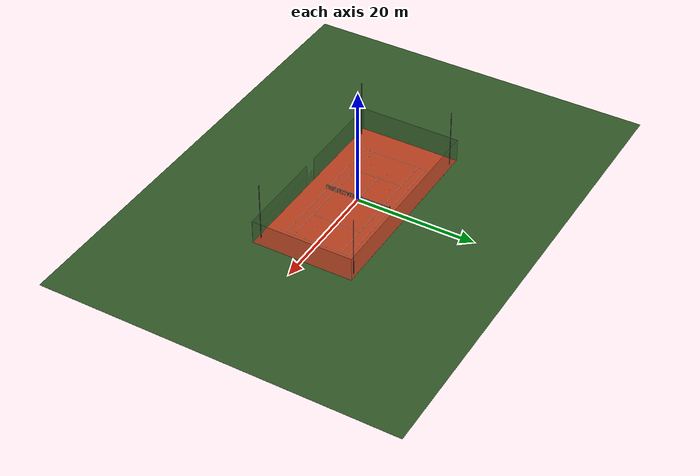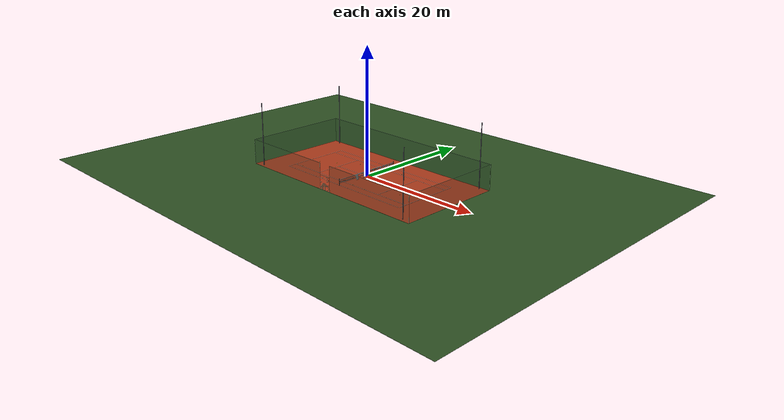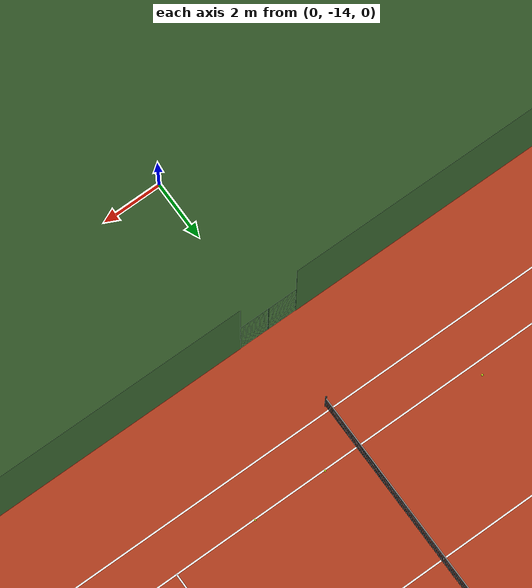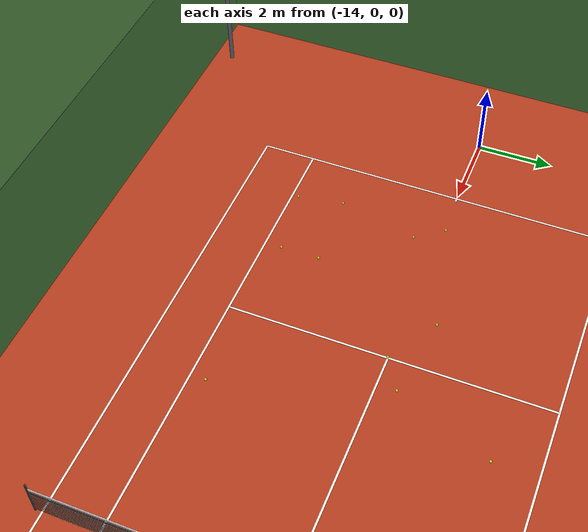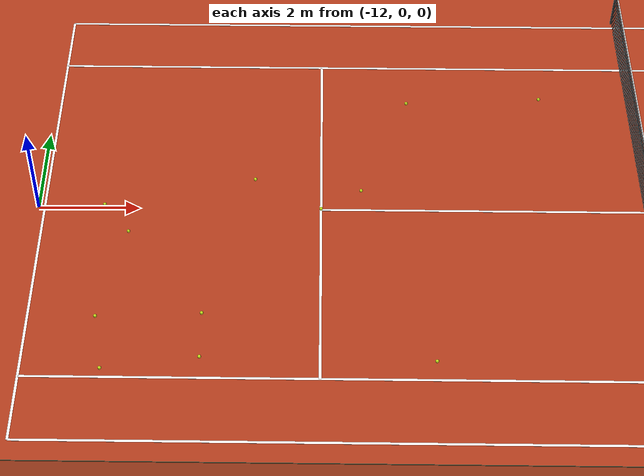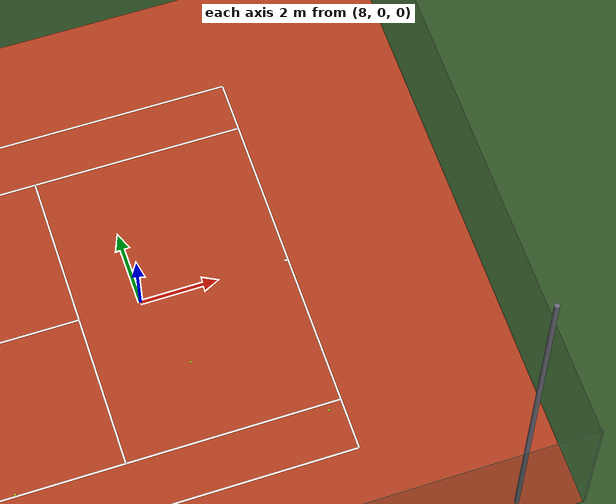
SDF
<?xml version="1.0"?>
<sdf version="1.9">
<world name="tennis_court">

  <physics name="ode" type="ode">
    <max_step_size>0.002</max_step_size>
    <real_time_factor>1.0</real_time_factor>
    <ode>
      <solver><type>quick</type><iters>100</iters><sor>1.3</sor></solver>
      <constraints>
        <cfm>0</cfm>
        <erp>0.2</erp>
        <contact_max_correcting_vel>2.0</contact_max_correcting_vel>
      </constraints>
    </ode>
  </physics>

  <!-- Required plugins -->
  <plugin filename="gz-sim-physics-system"       name="gz::sim::systems::Physics"/>
  <plugin filename="gz-sim-scene-broadcaster-system" name="gz::sim::systems::SceneBroadcaster"/>
  <plugin filename="gz-sim-user-commands-system"  name="gz::sim::systems::UserCommands"/>
  <plugin filename="gz-sim-sensors-system"        name="gz::sim::systems::Sensors">
    <render_engine>ogre</render_engine>
  </plugin>
  <plugin filename="gz-sim-imu-system"            name="gz::sim::systems::Imu"/>
  <plugin filename="gz-sim-contact-system"       name="gz::sim::systems::Contact"/>

  <!-- Morning sun ~10:00 — low angle, strong Mediterranean light, sharp shadows -->
  <light type="directional" name="sun">
    <cast_shadows>true</cast_shadows>
    <pose>0 0 100 0 0 0</pose>
    <diffuse>1.0 0.90 0.74 1</diffuse>
    <specular>0.28 0.22 0.14 1</specular>
    <direction>-0.55 0.30 -0.78</direction>
  </light>

  <!-- Cool sky fill (simulates light from the open sky opposite the sun) -->
  <light type="directional" name="sky_fill">
    <cast_shadows>false</cast_shadows>
    <pose>0 0 50 0 0 0</pose>
    <diffuse>0.22 0.30 0.46 1</diffuse>
    <specular>0.03 0.04 0.06 1</specular>
    <direction>0.45 -0.25 -0.86</direction>
  </light>

  <scene>
    <ambient>0.35 0.32 0.26 1</ambient>
    <background>0.58 0.72 0.90 1</background>
    <shadows>true</shadows>
    <grid>false</grid>
  </scene>

  <!-- Court -->
  <include>
    <uri>model://tennis_court</uri>
    <pose>0 0 0 0 0 0</pose>
  </include>

  <!-- ── TENNIS BALLS ── radius 0.033 m, mass 0.058 kg ─────────── -->
  <!-- Positions extracted from worlds/tennis_court.wbt -->
  <model name="ball_00"><pose>-4.264 -3.713 0.033 0 0 0</pose>
    <link name="ball"><inertial><mass>0.058</mass><inertia><ixx>2.5e-5</ixx><iyy>2.5e-5</iyy><izz>2.5e-5</izz></inertia></inertial>
    <collision name="col"><geometry><sphere><radius>0.033</radius></sphere></geometry><surface><friction><ode><mu>0.5</mu><mu2>0.5</mu2></ode></friction></surface></collision>
    <visual name="vis"><geometry><sphere><radius>0.033</radius></sphere></geometry><material><ambient>0.8 0.9 0.1 1</ambient><diffuse>0.8 0.9 0.1 1</diffuse></material></visual>
    </link></model>

  <model name="ball_01"><pose>3.647 -4.082 0.033 0 0 0</pose>
    <link name="ball"><inertial><mass>0.058</mass><inertia><ixx>2.5e-5</ixx><iyy>2.5e-5</iyy><izz>2.5e-5</izz></inertia></inertial>
    <collision name="col"><geometry><sphere><radius>0.033</radius></sphere></geometry><surface><friction><ode><mu>0.5</mu><mu2>0.5</mu2></ode></friction></surface></collision>
    <visual name="vis"><geometry><sphere><radius>0.033</radius></sphere></geometry><material><ambient>0.8 0.9 0.1 1</ambient><diffuse>0.8 0.9 0.1 1</diffuse></material></visual>
    </link></model>

  <model name="ball_02"><pose>-6.4 0.0 0.033 0 0 0</pose>
    <link name="ball"><inertial><mass>0.058</mass><inertia><ixx>2.5e-5</ixx><iyy>2.5e-5</iyy><izz>2.5e-5</izz></inertia></inertial>
    <collision name="col"><geometry><sphere><radius>0.033</radius></sphere></geometry><surface><friction><ode><mu>0.5</mu><mu2>0.5</mu2></ode></friction></surface></collision>
    <visual name="vis"><geometry><sphere><radius>0.033</radius></sphere></geometry><material><ambient>0.8 0.9 0.1 1</ambient><diffuse>0.8 0.9 0.1 1</diffuse></material></visual>
    </link></model>

  <model name="ball_03"><pose>-10.696 0.072 0.033 0 0 0</pose>
    <link name="ball"><inertial><mass>0.058</mass><inertia><ixx>2.5e-5</ixx><iyy>2.5e-5</iyy><izz>2.5e-5</izz></inertia></inertial>
    <collision name="col"><geometry><sphere><radius>0.033</radius></sphere></geometry><surface><friction><ode><mu>0.5</mu><mu2>0.5</mu2></ode></friction></surface></collision>
    <visual name="vis"><geometry><sphere><radius>0.033</radius></sphere></geometry><material><ambient>0.8 0.9 0.1 1</ambient><diffuse>0.8 0.9 0.1 1</diffuse></material></visual>
    </link></model>

  <model name="ball_04"><pose>-10.165 -0.632 0.033 0 0 0</pose>
    <link name="ball"><inertial><mass>0.058</mass><inertia><ixx>2.5e-5</ixx><iyy>2.5e-5</iyy><izz>2.5e-5</izz></inertia></inertial>
    <collision name="col"><geometry><sphere><radius>0.033</radius></sphere></geometry><surface><friction><ode><mu>0.5</mu><mu2>0.5</mu2></ode></friction></surface></collision>
    <visual name="vis"><geometry><sphere><radius>0.033</radius></sphere></geometry><material><ambient>0.8 0.9 0.1 1</ambient><diffuse>0.8 0.9 0.1 1</diffuse></material></visual>
    </link></model>

  <model name="ball_05"><pose>-10.409 -3.936 0.033 0 0 0</pose>
    <link name="ball"><inertial><mass>0.058</mass><inertia><ixx>2.5e-5</ixx><iyy>2.5e-5</iyy><izz>2.5e-5</izz></inertia></inertial>
    <collision name="col"><geometry><sphere><radius>0.033</radius></sphere></geometry><surface><friction><ode><mu>0.5</mu><mu2>0.5</mu2></ode></friction></surface></collision>
    <visual name="vis"><geometry><sphere><radius>0.033</radius></sphere></geometry><material><ambient>0.8 0.9 0.1 1</ambient><diffuse>0.8 0.9 0.1 1</diffuse></material></visual>
    </link></model>

  <model name="ball_06"><pose>-1.823 3.169 0.033 0 0 0</pose>
    <link name="ball"><inertial><mass>0.058</mass><inertia><ixx>2.5e-5</ixx><iyy>2.5e-5</iyy><izz>2.5e-5</izz></inertia></inertial>
    <collision name="col"><geometry><sphere><radius>0.033</radius></sphere></geometry><surface><friction><ode><mu>0.5</mu><mu2>0.5</mu2></ode></friction></surface></collision>
    <visual name="vis"><geometry><sphere><radius>0.033</radius></sphere></geometry><material><ambient>0.8 0.9 0.1 1</ambient><diffuse>0.8 0.9 0.1 1</diffuse></material></visual>
    </link></model>

  <model name="ball_07"><pose>-8.622 -2.648 0.033 0 0 0</pose>
    <link name="ball"><inertial><mass>0.058</mass><inertia><ixx>2.5e-5</ixx><iyy>2.5e-5</iyy><izz>2.5e-5</izz></inertia></inertial>
    <collision name="col"><geometry><sphere><radius>0.033</radius></sphere></geometry><surface><friction><ode><mu>0.5</mu><mu2>0.5</mu2></ode></friction></surface></collision>
    <visual name="vis"><geometry><sphere><radius>0.033</radius></sphere></geometry><material><ambient>0.8 0.9 0.1 1</ambient><diffuse>0.8 0.9 0.1 1</diffuse></material></visual>
    </link></model>

  <model name="ball_08"><pose>3.08 4.298 0.033 0 0 0</pose>
    <link name="ball"><inertial><mass>0.058</mass><inertia><ixx>2.5e-5</ixx><iyy>2.5e-5</iyy><izz>2.5e-5</izz></inertia></inertial>
    <collision name="col"><geometry><sphere><radius>0.033</radius></sphere></geometry><surface><friction><ode><mu>0.5</mu><mu2>0.5</mu2></ode></friction></surface></collision>
    <visual name="vis"><geometry><sphere><radius>0.033</radius></sphere></geometry><material><ambient>0.8 0.9 0.1 1</ambient><diffuse>0.8 0.9 0.1 1</diffuse></material></visual>
    </link></model>

  <model name="ball_09"><pose>-5.6 0.5 0.033 0 0 0</pose>
    <link name="ball"><inertial><mass>0.058</mass><inertia><ixx>2.5e-5</ixx><iyy>2.5e-5</iyy><izz>2.5e-5</izz></inertia></inertial>
    <collision name="col"><geometry><sphere><radius>0.033</radius></sphere></geometry><surface><friction><ode><mu>0.5</mu><mu2>0.5</mu2></ode></friction></surface></collision>
    <visual name="vis"><geometry><sphere><radius>0.033</radius></sphere></geometry><material><ambient>0.8 0.9 0.1 1</ambient><diffuse>0.8 0.9 0.1 1</diffuse></material></visual>
    </link></model>

  <model name="ball_10"><pose>11.513 -4.32 0.033 0 0 0</pose>
    <link name="ball"><inertial><mass>0.058</mass><inertia><ixx>2.5e-5</ixx><iyy>2.5e-5</iyy><izz>2.5e-5</izz></inertia></inertial>
    <collision name="col"><geometry><sphere><radius>0.033</radius></sphere></geometry><surface><friction><ode><mu>0.5</mu><mu2>0.5</mu2></ode></friction></surface></collision>
    <visual name="vis"><geometry><sphere><radius>0.033</radius></sphere></geometry><material><ambient>0.8 0.9 0.1 1</ambient><diffuse>0.8 0.9 0.1 1</diffuse></material></visual>
    </link></model>

  <model name="ball_11"><pose>8.692 -2.006 0.033 0 0 0</pose>
    <link name="ball"><inertial><mass>0.058</mass><inertia><ixx>2.5e-5</ixx><iyy>2.5e-5</iyy><izz>2.5e-5</izz></inertia></inertial>
    <collision name="col"><geometry><sphere><radius>0.033</radius></sphere></geometry><surface><friction><ode><mu>0.5</mu><mu2>0.5</mu2></ode></friction></surface></collision>
    <visual name="vis"><geometry><sphere><radius>0.033</radius></sphere></geometry><material><ambient>0.8 0.9 0.1 1</ambient><diffuse>0.8 0.9 0.1 1</diffuse></material></visual>
    </link></model>

  <model name="ball_12"><pose>-8.61 -3.661 0.033 0 0 0</pose>
    <link name="ball"><inertial><mass>0.058</mass><inertia><ixx>2.5e-5</ixx><iyy>2.5e-5</iyy><izz>2.5e-5</izz></inertia></inertial>
    <collision name="col"><geometry><sphere><radius>0.033</radius></sphere></geometry><surface><friction><ode><mu>0.5</mu><mu2>0.5</mu2></ode></friction></surface></collision>
    <visual name="vis"><geometry><sphere><radius>0.033</radius></sphere></geometry><material><ambient>0.8 0.9 0.1 1</ambient><diffuse>0.8 0.9 0.1 1</diffuse></material></visual>
    </link></model>

  <model name="ball_13"><pose>-4.623 3.009 0.033 0 0 0</pose>
    <link name="ball"><inertial><mass>0.058</mass><inertia><ixx>2.5e-5</ixx><iyy>2.5e-5</iyy><izz>2.5e-5</izz></inertia></inertial>
    <collision name="col"><geometry><sphere><radius>0.033</radius></sphere></geometry><surface><friction><ode><mu>0.5</mu><mu2>0.5</mu2></ode></friction></surface></collision>
    <visual name="vis"><geometry><sphere><radius>0.033</radius></sphere></geometry><material><ambient>0.8 0.9 0.1 1</ambient><diffuse>0.8 0.9 0.1 1</diffuse></material></visual>
    </link></model>

  <model name="ball_14"><pose>-7.725 0.784 0.033 0 0 0</pose>
    <link name="ball"><inertial><mass>0.058</mass><inertia><ixx>2.5e-5</ixx><iyy>2.5e-5</iyy><izz>2.5e-5</izz></inertia></inertial>
    <collision name="col"><geometry><sphere><radius>0.033</radius></sphere></geometry><surface><friction><ode><mu>0.5</mu><mu2>0.5</mu2></ode></friction></surface></collision>
    <visual name="vis"><geometry><sphere><radius>0.033</radius></sphere></geometry><material><ambient>0.8 0.9 0.1 1</ambient><diffuse>0.8 0.9 0.1 1</diffuse></material></visual>
    </link></model>

  <model name="ball_15"><pose>3.367 -1.17 0.033 0 0 0</pose>
    <link name="ball"><inertial><mass>0.058</mass><inertia><ixx>2.5e-5</ixx><iyy>2.5e-5</iyy><izz>2.5e-5</izz></inertia></inertial>
    <collision name="col"><geometry><sphere><radius>0.033</radius></sphere></geometry><surface><friction><ode><mu>0.5</mu><mu2>0.5</mu2></ode></friction></surface></collision>
    <visual name="vis"><geometry><sphere><radius>0.033</radius></sphere></geometry><material><ambient>0.8 0.9 0.1 1</ambient><diffuse>0.8 0.9 0.1 1</diffuse></material></visual>
    </link></model>

  <model name="ball_16"><pose>1.154 -4.081 0.033 0 0 0</pose>
    <link name="ball"><inertial><mass>0.058</mass><inertia><ixx>2.5e-5</ixx><iyy>2.5e-5</iyy><izz>2.5e-5</izz></inertia></inertial>
    <collision name="col"><geometry><sphere><radius>0.033</radius></sphere></geometry><surface><friction><ode><mu>0.5</mu><mu2>0.5</mu2></ode></friction></surface></collision>
    <visual name="vis"><geometry><sphere><radius>0.033</radius></sphere></geometry><material><ambient>0.8 0.9 0.1 1</ambient><diffuse>0.8 0.9 0.1 1</diffuse></material></visual>
    </link></model>

  <model name="ball_17"><pose>-10.608 -2.741 0.033 0 0 0</pose>
    <link name="ball"><inertial><mass>0.058</mass><inertia><ixx>2.5e-5</ixx><iyy>2.5e-5</iyy><izz>2.5e-5</izz></inertia></inertial>
    <collision name="col"><geometry><sphere><radius>0.033</radius></sphere></geometry><surface><friction><ode><mu>0.5</mu><mu2>0.5</mu2></ode></friction></surface></collision>
    <visual name="vis"><geometry><sphere><radius>0.033</radius></sphere></geometry><material><ambient>0.8 0.9 0.1 1</ambient><diffuse>0.8 0.9 0.1 1</diffuse></material></visual>
    </link></model>

</world>
</sdf>

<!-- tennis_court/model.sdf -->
<sdf version="1.9">
<model name="tennis_court">
  <static>true</static>

  <!-- Ã¢â€â‚¬Ã¢â€â‚¬ OUTER GROUND (grass/vegetation outside the fence) Ã¢â€â‚¬Ã¢â€â‚¬Ã¢â€â‚¬Ã¢â€â‚¬Ã¢â€â‚¬Ã¢â€â‚¬Ã¢â€â‚¬Ã¢â€â‚¬Ã¢â€â‚¬Ã¢â€â‚¬Ã¢â€â‚¬Ã¢â€â‚¬Ã¢â€â‚¬ -->
  <link name="outer_ground">
    <visual name="vis">
      <pose>0 0 -0.014 0 0 0</pose>
      <geometry><box><size>80 60 0.02</size></box></geometry>
      <material>
        <ambient>0.16 0.28 0.12 1</ambient>
        <diffuse>0.18 0.32 0.14 1</diffuse>
        <specular>0.02 0.04 0.02 1</specular>
      </material>
    </visual>
  </link>

  <link name="ground">
    <collision name="col">
      <!-- Match the visual's -0.01 offset: without it the physics surface
           sat 10 mm ABOVE the visible court, so balls/robot appeared to
           float (balls rested at z=0.043 instead of 0.033). -->
      <pose>0 0 -0.01 0 0 0</pose>
      <geometry><box><size>33.0 17.0 0.02</size></box></geometry>
      <!-- Clay court surface friction for wheel contact. -->
      <surface>
        <friction>
          <ode>
            <mu>1.5</mu>
            <mu2>1.5</mu2>
          </ode>
        </friction>
      </surface>
    </collision>
    <visual name="vis">
      <pose>0 0 -0.01 0 0 0</pose>
      <geometry><box><size>33.0 17.0 0.02</size></box></geometry>
      <material>
        <ambient>0.64 0.20 0.09 1</ambient>
        <diffuse>0.68 0.23 0.11 1</diffuse>
        <specular>0.08 0.08 0.08 1</specular>
      </material>
    </visual>
  </link>

  <link name="baseline_east"><pose>11.885 0 0.001 0 0 0</pose>
    <visual name="v"><geometry><box><size>0.05 10.97 0.003</size></box></geometry>
      <material><ambient>0.96 0.96 0.96 1</ambient><diffuse>0.96 0.96 0.96 1</diffuse></material></visual></link>
  <link name="baseline_west"><pose>-11.885 0 0.001 0 0 0</pose>
    <visual name="v"><geometry><box><size>0.05 10.97 0.003</size></box></geometry>
      <material><ambient>0.96 0.96 0.96 1</ambient><diffuse>0.96 0.96 0.96 1</diffuse></material></visual></link>
  <link name="doubles_sideline_north"><pose>0 5.485 0.001 0 0 0</pose>
    <visual name="v"><geometry><box><size>23.77 0.05 0.003</size></box></geometry>
      <material><ambient>0.96 0.96 0.96 1</ambient><diffuse>0.96 0.96 0.96 1</diffuse></material></visual></link>
  <link name="doubles_sideline_south"><pose>0 -5.485 0.001 0 0 0</pose>
    <visual name="v"><geometry><box><size>23.77 0.05 0.003</size></box></geometry>
      <material><ambient>0.96 0.96 0.96 1</ambient><diffuse>0.96 0.96 0.96 1</diffuse></material></visual></link>
  <link name="singles_sideline_north"><pose>0 4.115 0.001 0 0 0</pose>
    <visual name="v"><geometry><box><size>23.77 0.05 0.003</size></box></geometry>
      <material><ambient>0.96 0.96 0.96 1</ambient><diffuse>0.96 0.96 0.96 1</diffuse></material></visual></link>
  <link name="singles_sideline_south"><pose>0 -4.115 0.001 0 0 0</pose>
    <visual name="v"><geometry><box><size>23.77 0.05 0.003</size></box></geometry>
      <material><ambient>0.96 0.96 0.96 1</ambient><diffuse>0.96 0.96 0.96 1</diffuse></material></visual></link>
  <link name="service_line_east"><pose>6.4 0 0.001 0 0 0</pose>
    <visual name="v"><geometry><box><size>0.05 8.23 0.003</size></box></geometry>
      <material><ambient>0.96 0.96 0.96 1</ambient><diffuse>0.96 0.96 0.96 1</diffuse></material></visual></link>
  <link name="service_line_west"><pose>-6.4 0 0.001 0 0 0</pose>
    <visual name="v"><geometry><box><size>0.05 8.23 0.003</size></box></geometry>
      <material><ambient>0.96 0.96 0.96 1</ambient><diffuse>0.96 0.96 0.96 1</diffuse></material></visual></link>
  <link name="centre_service_line"><pose>0 0 0.001 0 0 0</pose>
    <visual name="v"><geometry><box><size>12.8 0.05 0.003</size></box></geometry>
      <material><ambient>0.96 0.96 0.96 1</ambient><diffuse>0.96 0.96 0.96 1</diffuse></material></visual></link>
  <link name="centre_mark_east"><pose>11.835 0 0.001 0 0 0</pose>
    <visual name="v"><geometry><box><size>0.10 0.05 0.003</size></box></geometry>
      <material><ambient>0.96 0.96 0.96 1</ambient><diffuse>0.96 0.96 0.96 1</diffuse></material></visual></link>
  <link name="centre_mark_west"><pose>-11.835 0 0.001 0 0 0</pose>
    <visual name="v"><geometry><box><size>0.10 0.05 0.003</size></box></geometry>
      <material><ambient>0.96 0.96 0.96 1</ambient><diffuse>0.96 0.96 0.96 1</diffuse></material></visual></link>

  <link name="net_post_north"><pose>0 5.65 0.535 0 0 0</pose>
    <collision name="col"><geometry><cylinder><radius>0.025</radius><length>1.07</length></cylinder></geometry></collision>
    <visual name="v"><geometry><cylinder><radius>0.025</radius><length>1.07</length></cylinder></geometry>
      <material><ambient>0.15 0.15 0.15 1</ambient><diffuse>0.2 0.2 0.2 1</diffuse><specular>0.4 0.4 0.4 1</specular></material></visual></link>
  <link name="net_post_south"><pose>0 -5.65 0.535 0 0 0</pose>
    <collision name="col"><geometry><cylinder><radius>0.025</radius><length>1.07</length></cylinder></geometry></collision>
    <visual name="v"><geometry><cylinder><radius>0.025</radius><length>1.07</length></cylinder></geometry>
      <material><ambient>0.15 0.15 0.15 1</ambient><diffuse>0.2 0.2 0.2 1</diffuse><specular>0.4 0.4 0.4 1</specular></material></visual></link>

  <link name="net_wall">
    <pose>0 0 0 0 0 -1.5708</pose>

    <!-- Collision box centred in local frame -->
    <collision name="col">
      <pose>0 0 0.457 0 0 0</pose>
      <geometry><box><size>11.3 0.02 0.914</size></box></geometry>
    </collision>

    <visual name="net_lidar_strand"><pose>0 0 0.713 0 0 0</pose><geometry><box><size>11.3 0.02 0.03</size></box></geometry><material><ambient>0.11373 0.11373 0.11373 1</ambient><diffuse>0.11373 0.11373 0.11373 1</diffuse><specular>0.08 0.08 0.08 1</specular></material></visual>

    <!-- Procedural net visual: 5 cm DAE mat_2 strand grid, visible to the camera. -->
    <visual name="net_h_01"><pose>0 0 0.05 0 0 0</pose><geometry><box><size>11.3 0.006 0.006</size></box></geometry><material><ambient>0.11373 0.11373 0.11373 1</ambient><diffuse>0.11373 0.11373 0.11373 1</diffuse><specular>0.08 0.08 0.08 1</specular></material></visual>
    <visual name="net_h_02"><pose>0 0 0.10 0 0 0</pose><geometry><box><size>11.3 0.006 0.006</size></box></geometry><material><ambient>0.11373 0.11373 0.11373 1</ambient><diffuse>0.11373 0.11373 0.11373 1</diffuse><specular>0.08 0.08 0.08 1</specular></material></visual>
    <visual name="net_h_03"><pose>0 0 0.15 0 0 0</pose><geometry><box><size>11.3 0.006 0.006</size></box></geometry><material><ambient>0.11373 0.11373 0.11373 1</ambient><diffuse>0.11373 0.11373 0.11373 1</diffuse><specular>0.08 0.08 0.08 1</specular></material></visual>
    <visual name="net_h_04"><pose>0 0 0.20 0 0 0</pose><geometry><box><size>11.3 0.006 0.006</size></box></geometry><material><ambient>0.11373 0.11373 0.11373 1</ambient><diffuse>0.11373 0.11373 0.11373 1</diffuse><specular>0.08 0.08 0.08 1</specular></material></visual>
    <visual name="net_h_05"><pose>0 0 0.25 0 0 0</pose><geometry><box><size>11.3 0.006 0.006</size></box></geometry><material><ambient>0.11373 0.11373 0.11373 1</ambient><diffuse>0.11373 0.11373 0.11373 1</diffuse><specular>0.08 0.08 0.08 1</specular></material></visual>
    <visual name="net_h_06"><pose>0 0 0.30 0 0 0</pose><geometry><box><size>11.3 0.006 0.006</size></box></geometry><material><ambient>0.11373 0.11373 0.11373 1</ambient><diffuse>0.11373 0.11373 0.11373 1</diffuse><specular>0.08 0.08 0.08 1</specular></material></visual>
    <visual name="net_h_07"><pose>0 0 0.35 0 0 0</pose><geometry><box><size>11.3 0.006 0.006</size></box></geometry><material><ambient>0.11373 0.11373 0.11373 1</ambient><diffuse>0.11373 0.11373 0.11373 1</diffuse><specular>0.08 0.08 0.08 1</specular></material></visual>
    <visual name="net_h_08"><pose>0 0 0.40 0 0 0</pose><geometry><box><size>11.3 0.006 0.006</size></box></geometry><material><ambient>0.11373 0.11373 0.11373 1</ambient><diffuse>0.11373 0.11373 0.11373 1</diffuse><specular>0.08 0.08 0.08 1</specular></material></visual>
    <visual name="net_h_09"><pose>0 0 0.45 0 0 0</pose><geometry><box><size>11.3 0.006 0.006</size></box></geometry><material><ambient>0.11373 0.11373 0.11373 1</ambient><diffuse>0.11373 0.11373 0.11373 1</diffuse><specular>0.08 0.08 0.08 1</specular></material></visual>
    <visual name="net_h_10"><pose>0 0 0.50 0 0 0</pose><geometry><box><size>11.3 0.006 0.006</size></box></geometry><material><ambient>0.11373 0.11373 0.11373 1</ambient><diffuse>0.11373 0.11373 0.11373 1</diffuse><specular>0.08 0.08 0.08 1</specular></material></visual>
    <visual name="net_h_11"><pose>0 0 0.55 0 0 0</pose><geometry><box><size>11.3 0.006 0.006</size></box></geometry><material><ambient>0.11373 0.11373 0.11373 1</ambient><diffuse>0.11373 0.11373 0.11373 1</diffuse><specular>0.08 0.08 0.08 1</specular></material></visual>
    <visual name="net_h_12"><pose>0 0 0.60 0 0 0</pose><geometry><box><size>11.3 0.006 0.006</size></box></geometry><material><ambient>0.11373 0.11373 0.11373 1</ambient><diffuse>0.11373 0.11373 0.11373 1</diffuse><specular>0.08 0.08 0.08 1</specular></material></visual>
    <visual name="net_h_13"><pose>0 0 0.65 0 0 0</pose><geometry><box><size>11.3 0.006 0.006</size></box></geometry><material><ambient>0.11373 0.11373 0.11373 1</ambient><diffuse>0.11373 0.11373 0.11373 1</diffuse><specular>0.08 0.08 0.08 1</specular></material></visual>
    <visual name="net_h_14"><pose>0 0 0.70 0 0 0</pose><geometry><box><size>11.3 0.006 0.006</size></box></geometry><material><ambient>0.11373 0.11373 0.11373 1</ambient><diffuse>0.11373 0.11373 0.11373 1</diffuse><specular>0.08 0.08 0.08 1</specular></material></visual>
    <visual name="net_h_15"><pose>0 0 0.75 0 0 0</pose><geometry><box><size>11.3 0.006 0.006</size></box></geometry><material><ambient>0.11373 0.11373 0.11373 1</ambient><diffuse>0.11373 0.11373 0.11373 1</diffuse><specular>0.08 0.08 0.08 1</specular></material></visual>
    <visual name="net_h_16"><pose>0 0 0.80 0 0 0</pose><geometry><box><size>11.3 0.006 0.006</size></box></geometry><material><ambient>0.11373 0.11373 0.11373 1</ambient><diffuse>0.11373 0.11373 0.11373 1</diffuse><specular>0.08 0.08 0.08 1</specular></material></visual>
    <visual name="net_h_17"><pose>0 0 0.85 0 0 0</pose><geometry><box><size>11.3 0.006 0.006</size></box></geometry><material><ambient>0.11373 0.11373 0.11373 1</ambient><diffuse>0.11373 0.11373 0.11373 1</diffuse><specular>0.08 0.08 0.08 1</specular></material></visual>
    <visual name="net_v_001"><pose>-5.25 0 0.43 0 0 0</pose><geometry><box><size>0.006 0.006 0.86</size></box></geometry><material><ambient>0.11373 0.11373 0.11373 1</ambient><diffuse>0.11373 0.11373 0.11373 1</diffuse><specular>0.08 0.08 0.08 1</specular></material></visual>
    <visual name="net_v_002"><pose>-5.20 0 0.43 0 0 0</pose><geometry><box><size>0.006 0.006 0.86</size></box></geometry><material><ambient>0.11373 0.11373 0.11373 1</ambient><diffuse>0.11373 0.11373 0.11373 1</diffuse><specular>0.08 0.08 0.08 1</specular></material></visual>
    <visual name="net_v_003"><pose>-5.15 0 0.43 0 0 0</pose><geometry><box><size>0.006 0.006 0.86</size></box></geometry><material><ambient>0.11373 0.11373 0.11373 1</ambient><diffuse>0.11373 0.11373 0.11373 1</diffuse><specular>0.08 0.08 0.08 1</specular></material></visual>
    <visual name="net_v_004"><pose>-5.10 0 0.43 0 0 0</pose><geometry><box><size>0.006 0.006 0.86</size></box></geometry><material><ambient>0.11373 0.11373 0.11373 1</ambient><diffuse>0.11373 0.11373 0.11373 1</diffuse><specular>0.08 0.08 0.08 1</specular></material></visual>
    <visual name="net_v_005"><pose>-5.05 0 0.43 0 0 0</pose><geometry><box><size>0.006 0.006 0.86</size></box></geometry><material><ambient>0.11373 0.11373 0.11373 1</ambient><diffuse>0.11373 0.11373 0.11373 1</diffuse><specular>0.08 0.08 0.08 1</specular></material></visual>
    <visual name="net_v_006"><pose>-5.00 0 0.43 0 0 0</pose><geometry><box><size>0.006 0.006 0.86</size></box></geometry><material><ambient>0.11373 0.11373 0.11373 1</ambient><diffuse>0.11373 0.11373 0.11373 1</diffuse><specular>0.08 0.08 0.08 1</specular></material></visual>
    <visual name="net_v_007"><pose>-4.95 0 0.43 0 0 0</pose><geometry><box><size>0.006 0.006 0.86</size></box></geometry><material><ambient>0.11373 0.11373 0.11373 1</ambient><diffuse>0.11373 0.11373 0.11373 1</diffuse><specular>0.08 0.08 0.08 1</specular></material></visual>
    <visual name="net_v_008"><pose>-4.90 0 0.43 0 0 0</pose><geometry><box><size>0.006 0.006 0.86</size></box></geometry><material><ambient>0.11373 0.11373 0.11373 1</ambient><diffuse>0.11373 0.11373 0.11373 1</diffuse><specular>0.08 0.08 0.08 1</specular></material></visual>
    <visual name="net_v_009"><pose>-4.85 0 0.43 0 0 0</pose><geometry><box><size>0.006 0.006 0.86</size></box></geometry><material><ambient>0.11373 0.11373 0.11373 1</ambient><diffuse>0.11373 0.11373 0.11373 1</diffuse><specular>0.08 0.08 0.08 1</specular></material></visual>
    <visual name="net_v_010"><pose>-4.80 0 0.43 0 0 0</pose><geometry><box><size>0.006 0.006 0.86</size></box></geometry><material><ambient>0.11373 0.11373 0.11373 1</ambient><diffuse>0.11373 0.11373 0.11373 1</diffuse><specular>0.08 0.08 0.08 1</specular></material></visual>
    <visual name="net_v_011"><pose>-4.75 0 0.43 0 0 0</pose><geometry><box><size>0.006 0.006 0.86</size></box></geometry><material><ambient>0.11373 0.11373 0.11373 1</ambient><diffuse>0.11373 0.11373 0.11373 1</diffuse><specular>0.08 0.08 0.08 1</specular></material></visual>
    <visual name="net_v_012"><pose>-4.70 0 0.43 0 0 0</pose><geometry><box><size>0.006 0.006 0.86</size></box></geometry><material><ambient>0.11373 0.11373 0.11373 1</ambient><diffuse>0.11373 0.11373 0.11373 1</diffuse><specular>0.08 0.08 0.08 1</specular></material></visual>
    <visual name="net_v_013"><pose>-4.65 0 0.43 0 0 0</pose><geometry><box><size>0.006 0.006 0.86</size></box></geometry><material><ambient>0.11373 0.11373 0.11373 1</ambient><diffuse>0.11373 0.11373 0.11373 1</diffuse><specular>0.08 0.08 0.08 1</specular></material></visual>
    <visual name="net_v_014"><pose>-4.60 0 0.43 0 0 0</pose><geometry><box><size>0.006 0.006 0.86</size></box></geometry><material><ambient>0.11373 0.11373 0.11373 1</ambient><diffuse>0.11373 0.11373 0.11373 1</diffuse><specular>0.08 0.08 0.08 1</specular></material></visual>
    <visual name="net_v_015"><pose>-4.55 0 0.43 0 0 0</pose><geometry><box><size>0.006 0.006 0.86</size></box></geometry><material><ambient>0.11373 0.11373 0.11373 1</ambient><diffuse>0.11373 0.11373 0.11373 1</diffuse><specular>0.08 0.08 0.08 1</specular></material></visual>
    <visual name="net_v_016"><pose>-4.50 0 0.43 0 0 0</pose><geometry><box><size>0.006 0.006 0.86</size></box></geometry><material><ambient>0.11373 0.11373 0.11373 1</ambient><diffuse>0.11373 0.11373 0.11373 1</diffuse><specular>0.08 0.08 0.08 1</specular></material></visual>
    <visual name="net_v_017"><pose>-4.45 0 0.43 0 0 0</pose><geometry><box><size>0.006 0.006 0.86</size></box></geometry><material><ambient>0.11373 0.11373 0.11373 1</ambient><diffuse>0.11373 0.11373 0.11373 1</diffuse><specular>0.08 0.08 0.08 1</specular></material></visual>
    <visual name="net_v_018"><pose>-4.40 0 0.43 0 0 0</pose><geometry><box><size>0.006 0.006 0.86</size></box></geometry><material><ambient>0.11373 0.11373 0.11373 1</ambient><diffuse>0.11373 0.11373 0.11373 1</diffuse><specular>0.08 0.08 0.08 1</specular></material></visual>
    <visual name="net_v_019"><pose>-4.35 0 0.43 0 0 0</pose><geometry><box><size>0.006 0.006 0.86</size></box></geometry><material><ambient>0.11373 0.11373 0.11373 1</ambient><diffuse>0.11373 0.11373 0.11373 1</diffuse><specular>0.08 0.08 0.08 1</specular></material></visual>
    <visual name="net_v_020"><pose>-4.30 0 0.43 0 0 0</pose><geometry><box><size>0.006 0.006 0.86</size></box></geometry><material><ambient>0.11373 0.11373 0.11373 1</ambient><diffuse>0.11373 0.11373 0.11373 1</diffuse><specular>0.08 0.08 0.08 1</specular></material></visual>
    <visual name="net_v_021"><pose>-4.25 0 0.43 0 0 0</pose><geometry><box><size>0.006 0.006 0.86</size></box></geometry><material><ambient>0.11373 0.11373 0.11373 1</ambient><diffuse>0.11373 0.11373 0.11373 1</diffuse><specular>0.08 0.08 0.08 1</specular></material></visual>
    <visual name="net_v_022"><pose>-4.20 0 0.43 0 0 0</pose><geometry><box><size>0.006 0.006 0.86</size></box></geometry><material><ambient>0.11373 0.11373 0.11373 1</ambient><diffuse>0.11373 0.11373 0.11373 1</diffuse><specular>0.08 0.08 0.08 1</specular></material></visual>
    <visual name="net_v_023"><pose>-4.15 0 0.43 0 0 0</pose><geometry><box><size>0.006 0.006 0.86</size></box></geometry><material><ambient>0.11373 0.11373 0.11373 1</ambient><diffuse>0.11373 0.11373 0.11373 1</diffuse><specular>0.08 0.08 0.08 1</specular></material></visual>
    <visual name="net_v_024"><pose>-4.10 0 0.43 0 0 0</pose><geometry><box><size>0.006 0.006 0.86</size></box></geometry><material><ambient>0.11373 0.11373 0.11373 1</ambient><diffuse>0.11373 0.11373 0.11373 1</diffuse><specular>0.08 0.08 0.08 1</specular></material></visual>
    <visual name="net_v_025"><pose>-4.05 0 0.43 0 0 0</pose><geometry><box><size>0.006 0.006 0.86</size></box></geometry><material><ambient>0.11373 0.11373 0.11373 1</ambient><diffuse>0.11373 0.11373 0.11373 1</diffuse><specular>0.08 0.08 0.08 1</specular></material></visual>
    <visual name="net_v_026"><pose>-4.00 0 0.43 0 0 0</pose><geometry><box><size>0.006 0.006 0.86</size></box></geometry><material><ambient>0.11373 0.11373 0.11373 1</ambient><diffuse>0.11373 0.11373 0.11373 1</diffuse><specular>0.08 0.08 0.08 1</specular></material></visual>
    <visual name="net_v_027"><pose>-3.95 0 0.43 0 0 0</pose><geometry><box><size>0.006 0.006 0.86</size></box></geometry><material><ambient>0.11373 0.11373 0.11373 1</ambient><diffuse>0.11373 0.11373 0.11373 1</diffuse><specular>0.08 0.08 0.08 1</specular></material></visual>
    <visual name="net_v_028"><pose>-3.90 0 0.43 0 0 0</pose><geometry><box><size>0.006 0.006 0.86</size></box></geometry><material><ambient>0.11373 0.11373 0.11373 1</ambient><diffuse>0.11373 0.11373 0.11373 1</diffuse><specular>0.08 0.08 0.08 1</specular></material></visual>
    <visual name="net_v_029"><pose>-3.85 0 0.43 0 0 0</pose><geometry><box><size>0.006 0.006 0.86</size></box></geometry><material><ambient>0.11373 0.11373 0.11373 1</ambient><diffuse>0.11373 0.11373 0.11373 1</diffuse><specular>0.08 0.08 0.08 1</specular></material></visual>
    <visual name="net_v_030"><pose>-3.80 0 0.43 0 0 0</pose><geometry><box><size>0.006 0.006 0.86</size></box></geometry><material><ambient>0.11373 0.11373 0.11373 1</ambient><diffuse>0.11373 0.11373 0.11373 1</diffuse><specular>0.08 0.08 0.08 1</specular></material></visual>
    <visual name="net_v_031"><pose>-3.75 0 0.43 0 0 0</pose><geometry><box><size>0.006 0.006 0.86</size></box></geometry><material><ambient>0.11373 0.11373 0.11373 1</ambient><diffuse>0.11373 0.11373 0.11373 1</diffuse><specular>0.08 0.08 0.08 1</specular></material></visual>
    <visual name="net_v_032"><pose>-3.70 0 0.43 0 0 0</pose><geometry><box><size>0.006 0.006 0.86</size></box></geometry><material><ambient>0.11373 0.11373 0.11373 1</ambient><diffuse>0.11373 0.11373 0.11373 1</diffuse><specular>0.08 0.08 0.08 1</specular></material></visual>
    <visual name="net_v_033"><pose>-3.65 0 0.43 0 0 0</pose><geometry><box><size>0.006 0.006 0.86</size></box></geometry><material><ambient>0.11373 0.11373 0.11373 1</ambient><diffuse>0.11373 0.11373 0.11373 1</diffuse><specular>0.08 0.08 0.08 1</specular></material></visual>
    <visual name="net_v_034"><pose>-3.60 0 0.43 0 0 0</pose><geometry><box><size>0.006 0.006 0.86</size></box></geometry><material><ambient>0.11373 0.11373 0.11373 1</ambient><diffuse>0.11373 0.11373 0.11373 1</diffuse><specular>0.08 0.08 0.08 1</specular></material></visual>
    <visual name="net_v_035"><pose>-3.55 0 0.43 0 0 0</pose><geometry><box><size>0.006 0.006 0.86</size></box></geometry><material><ambient>0.11373 0.11373 0.11373 1</ambient><diffuse>0.11373 0.11373 0.11373 1</diffuse><specular>0.08 0.08 0.08 1</specular></material></visual>
    <visual name="net_v_036"><pose>-3.50 0 0.43 0 0 0</pose><geometry><box><size>0.006 0.006 0.86</size></box></geometry><material><ambient>0.11373 0.11373 0.11373 1</ambient><diffuse>0.11373 0.11373 0.11373 1</diffuse><specular>0.08 0.08 0.08 1</specular></material></visual>
    <visual name="net_v_037"><pose>-3.45 0 0.43 0 0 0</pose><geometry><box><size>0.006 0.006 0.86</size></box></geometry><material><ambient>0.11373 0.11373 0.11373 1</ambient><diffuse>0.11373 0.11373 0.11373 1</diffuse><specular>0.08 0.08 0.08 1</specular></material></visual>
    <visual name="net_v_038"><pose>-3.40 0 0.43 0 0 0</pose><geometry><box><size>0.006 0.006 0.86</size></box></geometry><material><ambient>0.11373 0.11373 0.11373 1</ambient><diffuse>0.11373 0.11373 0.11373 1</diffuse><specular>0.08 0.08 0.08 1</specular></material></visual>
    <visual name="net_v_039"><pose>-3.35 0 0.43 0 0 0</pose><geometry><box><size>0.006 0.006 0.86</size></box></geometry><material><ambient>0.11373 0.11373 0.11373 1</ambient><diffuse>0.11373 0.11373 0.11373 1</diffuse><specular>0.08 0.08 0.08 1</specular></material></visual>
    <visual name="net_v_040"><pose>-3.30 0 0.43 0 0 0</pose><geometry><box><size>0.006 0.006 0.86</size></box></geometry><material><ambient>0.11373 0.11373 0.11373 1</ambient><diffuse>0.11373 0.11373 0.11373 1</diffuse><specular>0.08 0.08 0.08 1</specular></material></visual>
    <visual name="net_v_041"><pose>-3.25 0 0.43 0 0 0</pose><geometry><box><size>0.006 0.006 0.86</size></box></geometry><material><ambient>0.11373 0.11373 0.11373 1</ambient><diffuse>0.11373 0.11373 0.11373 1</diffuse><specular>0.08 0.08 0.08 1</specular></material></visual>
    <visual name="net_v_042"><pose>-3.20 0 0.43 0 0 0</pose><geometry><box><size>0.006 0.006 0.86</size></box></geometry><material><ambient>0.11373 0.11373 0.11373 1</ambient><diffuse>0.11373 0.11373 0.11373 1</diffuse><specular>0.08 0.08 0.08 1</specular></material></visual>
    <visual name="net_v_043"><pose>-3.15 0 0.43 0 0 0</pose><geometry><box><size>0.006 0.006 0.86</size></box></geometry><material><ambient>0.11373 0.11373 0.11373 1</ambient><diffuse>0.11373 0.11373 0.11373 1</diffuse><specular>0.08 0.08 0.08 1</specular></material></visual>
    <visual name="net_v_044"><pose>-3.10 0 0.43 0 0 0</pose><geometry><box><size>0.006 0.006 0.86</size></box></geometry><material><ambient>0.11373 0.11373 0.11373 1</ambient><diffuse>0.11373 0.11373 0.11373 1</diffuse><specular>0.08 0.08 0.08 1</specular></material></visual>
    <visual name="net_v_045"><pose>-3.05 0 0.43 0 0 0</pose><geometry><box><size>0.006 0.006 0.86</size></box></geometry><material><ambient>0.11373 0.11373 0.11373 1</ambient><diffuse>0.11373 0.11373 0.11373 1</diffuse><specular>0.08 0.08 0.08 1</specular></material></visual>
    <visual name="net_v_046"><pose>-3.00 0 0.43 0 0 0</pose><geometry><box><size>0.006 0.006 0.86</size></box></geometry><material><ambient>0.11373 0.11373 0.11373 1</ambient><diffuse>0.11373 0.11373 0.11373 1</diffuse><specular>0.08 0.08 0.08 1</specular></material></visual>
    <visual name="net_v_047"><pose>-2.95 0 0.43 0 0 0</pose><geometry><box><size>0.006 0.006 0.86</size></box></geometry><material><ambient>0.11373 0.11373 0.11373 1</ambient><diffuse>0.11373 0.11373 0.11373 1</diffuse><specular>0.08 0.08 0.08 1</specular></material></visual>
    <visual name="net_v_048"><pose>-2.90 0 0.43 0 0 0</pose><geometry><box><size>0.006 0.006 0.86</size></box></geometry><material><ambient>0.11373 0.11373 0.11373 1</ambient><diffuse>0.11373 0.11373 0.11373 1</diffuse><specular>0.08 0.08 0.08 1</specular></material></visual>
    <visual name="net_v_049"><pose>-2.85 0 0.43 0 0 0</pose><geometry><box><size>0.006 0.006 0.86</size></box></geometry><material><ambient>0.11373 0.11373 0.11373 1</ambient><diffuse>0.11373 0.11373 0.11373 1</diffuse><specular>0.08 0.08 0.08 1</specular></material></visual>
    <visual name="net_v_050"><pose>-2.80 0 0.43 0 0 0</pose><geometry><box><size>0.006 0.006 0.86</size></box></geometry><material><ambient>0.11373 0.11373 0.11373 1</ambient><diffuse>0.11373 0.11373 0.11373 1</diffuse><specular>0.08 0.08 0.08 1</specular></material></visual>
    <visual name="net_v_051"><pose>-2.75 0 0.43 0 0 0</pose><geometry><box><size>0.006 0.006 0.86</size></box></geometry><material><ambient>0.11373 0.11373 0.11373 1</ambient><diffuse>0.11373 0.11373 0.11373 1</diffuse><specular>0.08 0.08 0.08 1</specular></material></visual>
    <visual name="net_v_052"><pose>-2.70 0 0.43 0 0 0</pose><geometry><box><size>0.006 0.006 0.86</size></box></geometry><material><ambient>0.11373 0.11373 0.11373 1</ambient><diffuse>0.11373 0.11373 0.11373 1</diffuse><specular>0.08 0.08 0.08 1</specular></material></visual>
    <visual name="net_v_053"><pose>-2.65 0 0.43 0 0 0</pose><geometry><box><size>0.006 0.006 0.86</size></box></geometry><material><ambient>0.11373 0.11373 0.11373 1</ambient><diffuse>0.11373 0.11373 0.11373 1</diffuse><specular>0.08 0.08 0.08 1</specular></material></visual>
    <visual name="net_v_054"><pose>-2.60 0 0.43 0 0 0</pose><geometry><box><size>0.006 0.006 0.86</size></box></geometry><material><ambient>0.11373 0.11373 0.11373 1</ambient><diffuse>0.11373 0.11373 0.11373 1</diffuse><specular>0.08 0.08 0.08 1</specular></material></visual>
    <visual name="net_v_055"><pose>-2.55 0 0.43 0 0 0</pose><geometry><box><size>0.006 0.006 0.86</size></box></geometry><material><ambient>0.11373 0.11373 0.11373 1</ambient><diffuse>0.11373 0.11373 0.11373 1</diffuse><specular>0.08 0.08 0.08 1</specular></material></visual>
    <visual name="net_v_056"><pose>-2.50 0 0.43 0 0 0</pose><geometry><box><size>0.006 0.006 0.86</size></box></geometry><material><ambient>0.11373 0.11373 0.11373 1</ambient><diffuse>0.11373 0.11373 0.11373 1</diffuse><specular>0.08 0.08 0.08 1</specular></material></visual>
    <visual name="net_v_057"><pose>-2.45 0 0.43 0 0 0</pose><geometry><box><size>0.006 0.006 0.86</size></box></geometry><material><ambient>0.11373 0.11373 0.11373 1</ambient><diffuse>0.11373 0.11373 0.11373 1</diffuse><specular>0.08 0.08 0.08 1</specular></material></visual>
    <visual name="net_v_058"><pose>-2.40 0 0.43 0 0 0</pose><geometry><box><size>0.006 0.006 0.86</size></box></geometry><material><ambient>0.11373 0.11373 0.11373 1</ambient><diffuse>0.11373 0.11373 0.11373 1</diffuse><specular>0.08 0.08 0.08 1</specular></material></visual>
    <visual name="net_v_059"><pose>-2.35 0 0.43 0 0 0</pose><geometry><box><size>0.006 0.006 0.86</size></box></geometry><material><ambient>0.11373 0.11373 0.11373 1</ambient><diffuse>0.11373 0.11373 0.11373 1</diffuse><specular>0.08 0.08 0.08 1</specular></material></visual>
    <visual name="net_v_060"><pose>-2.30 0 0.43 0 0 0</pose><geometry><box><size>0.006 0.006 0.86</size></box></geometry><material><ambient>0.11373 0.11373 0.11373 1</ambient><diffuse>0.11373 0.11373 0.11373 1</diffuse><specular>0.08 0.08 0.08 1</specular></material></visual>
    <visual name="net_v_061"><pose>-2.25 0 0.43 0 0 0</pose><geometry><box><size>0.006 0.006 0.86</size></box></geometry><material><ambient>0.11373 0.11373 0.11373 1</ambient><diffuse>0.11373 0.11373 0.11373 1</diffuse><specular>0.08 0.08 0.08 1</specular></material></visual>
    <visual name="net_v_062"><pose>-2.20 0 0.43 0 0 0</pose><geometry><box><size>0.006 0.006 0.86</size></box></geometry><material><ambient>0.11373 0.11373 0.11373 1</ambient><diffuse>0.11373 0.11373 0.11373 1</diffuse><specular>0.08 0.08 0.08 1</specular></material></visual>
    <visual name="net_v_063"><pose>-2.15 0 0.43 0 0 0</pose><geometry><box><size>0.006 0.006 0.86</size></box></geometry><material><ambient>0.11373 0.11373 0.11373 1</ambient><diffuse>0.11373 0.11373 0.11373 1</diffuse><specular>0.08 0.08 0.08 1</specular></material></visual>
    <visual name="net_v_064"><pose>-2.10 0 0.43 0 0 0</pose><geometry><box><size>0.006 0.006 0.86</size></box></geometry><material><ambient>0.11373 0.11373 0.11373 1</ambient><diffuse>0.11373 0.11373 0.11373 1</diffuse><specular>0.08 0.08 0.08 1</specular></material></visual>
    <visual name="net_v_065"><pose>-2.05 0 0.43 0 0 0</pose><geometry><box><size>0.006 0.006 0.86</size></box></geometry><material><ambient>0.11373 0.11373 0.11373 1</ambient><diffuse>0.11373 0.11373 0.11373 1</diffuse><specular>0.08 0.08 0.08 1</specular></material></visual>
    <visual name="net_v_066"><pose>-2.00 0 0.43 0 0 0</pose><geometry><box><size>0.006 0.006 0.86</size></box></geometry><material><ambient>0.11373 0.11373 0.11373 1</ambient><diffuse>0.11373 0.11373 0.11373 1</diffuse><specular>0.08 0.08 0.08 1</specular></material></visual>
    <visual name="net_v_067"><pose>-1.95 0 0.43 0 0 0</pose><geometry><box><size>0.006 0.006 0.86</size></box></geometry><material><ambient>0.11373 0.11373 0.11373 1</ambient><diffuse>0.11373 0.11373 0.11373 1</diffuse><specular>0.08 0.08 0.08 1</specular></material></visual>
    <visual name="net_v_068"><pose>-1.90 0 0.43 0 0 0</pose><geometry><box><size>0.006 0.006 0.86</size></box></geometry><material><ambient>0.11373 0.11373 0.11373 1</ambient><diffuse>0.11373 0.11373 0.11373 1</diffuse><specular>0.08 0.08 0.08 1</specular></material></visual>
    <visual name="net_v_069"><pose>-1.85 0 0.43 0 0 0</pose><geometry><box><size>0.006 0.006 0.86</size></box></geometry><material><ambient>0.11373 0.11373 0.11373 1</ambient><diffuse>0.11373 0.11373 0.11373 1</diffuse><specular>0.08 0.08 0.08 1</specular></material></visual>
    <visual name="net_v_070"><pose>-1.80 0 0.43 0 0 0</pose><geometry><box><size>0.006 0.006 0.86</size></box></geometry><material><ambient>0.11373 0.11373 0.11373 1</ambient><diffuse>0.11373 0.11373 0.11373 1</diffuse><specular>0.08 0.08 0.08 1</specular></material></visual>
    <visual name="net_v_071"><pose>-1.75 0 0.43 0 0 0</pose><geometry><box><size>0.006 0.006 0.86</size></box></geometry><material><ambient>0.11373 0.11373 0.11373 1</ambient><diffuse>0.11373 0.11373 0.11373 1</diffuse><specular>0.08 0.08 0.08 1</specular></material></visual>
    <visual name="net_v_072"><pose>-1.70 0 0.43 0 0 0</pose><geometry><box><size>0.006 0.006 0.86</size></box></geometry><material><ambient>0.11373 0.11373 0.11373 1</ambient><diffuse>0.11373 0.11373 0.11373 1</diffuse><specular>0.08 0.08 0.08 1</specular></material></visual>
    <visual name="net_v_073"><pose>-1.65 0 0.43 0 0 0</pose><geometry><box><size>0.006 0.006 0.86</size></box></geometry><material><ambient>0.11373 0.11373 0.11373 1</ambient><diffuse>0.11373 0.11373 0.11373 1</diffuse><specular>0.08 0.08 0.08 1</specular></material></visual>
    <visual name="net_v_074"><pose>-1.60 0 0.43 0 0 0</pose><geometry><box><size>0.006 0.006 0.86</size></box></geometry><material><ambient>0.11373 0.11373 0.11373 1</ambient><diffuse>0.11373 0.11373 0.11373 1</diffuse><specular>0.08 0.08 0.08 1</specular></material></visual>
    <visual name="net_v_075"><pose>-1.55 0 0.43 0 0 0</pose><geometry><box><size>0.006 0.006 0.86</size></box></geometry><material><ambient>0.11373 0.11373 0.11373 1</ambient><diffuse>0.11373 0.11373 0.11373 1</diffuse><specular>0.08 0.08 0.08 1</specular></material></visual>
    <visual name="net_v_076"><pose>-1.50 0 0.43 0 0 0</pose><geometry><box><size>0.006 0.006 0.86</size></box></geometry><material><ambient>0.11373 0.11373 0.11373 1</ambient><diffuse>0.11373 0.11373 0.11373 1</diffuse><specular>0.08 0.08 0.08 1</specular></material></visual>
    <visual name="net_v_077"><pose>-1.45 0 0.43 0 0 0</pose><geometry><box><size>0.006 0.006 0.86</size></box></geometry><material><ambient>0.11373 0.11373 0.11373 1</ambient><diffuse>0.11373 0.11373 0.11373 1</diffuse><specular>0.08 0.08 0.08 1</specular></material></visual>
    <visual name="net_v_078"><pose>-1.40 0 0.43 0 0 0</pose><geometry><box><size>0.006 0.006 0.86</size></box></geometry><material><ambient>0.11373 0.11373 0.11373 1</ambient><diffuse>0.11373 0.11373 0.11373 1</diffuse><specular>0.08 0.08 0.08 1</specular></material></visual>
    <visual name="net_v_079"><pose>-1.35 0 0.43 0 0 0</pose><geometry><box><size>0.006 0.006 0.86</size></box></geometry><material><ambient>0.11373 0.11373 0.11373 1</ambient><diffuse>0.11373 0.11373 0.11373 1</diffuse><specular>0.08 0.08 0.08 1</specular></material></visual>
    <visual name="net_v_080"><pose>-1.30 0 0.43 0 0 0</pose><geometry><box><size>0.006 0.006 0.86</size></box></geometry><material><ambient>0.11373 0.11373 0.11373 1</ambient><diffuse>0.11373 0.11373 0.11373 1</diffuse><specular>0.08 0.08 0.08 1</specular></material></visual>
    <visual name="net_v_081"><pose>-1.25 0 0.43 0 0 0</pose><geometry><box><size>0.006 0.006 0.86</size></box></geometry><material><ambient>0.11373 0.11373 0.11373 1</ambient><diffuse>0.11373 0.11373 0.11373 1</diffuse><specular>0.08 0.08 0.08 1</specular></material></visual>
    <visual name="net_v_082"><pose>-1.20 0 0.43 0 0 0</pose><geometry><box><size>0.006 0.006 0.86</size></box></geometry><material><ambient>0.11373 0.11373 0.11373 1</ambient><diffuse>0.11373 0.11373 0.11373 1</diffuse><specular>0.08 0.08 0.08 1</specular></material></visual>
    <visual name="net_v_083"><pose>-1.15 0 0.43 0 0 0</pose><geometry><box><size>0.006 0.006 0.86</size></box></geometry><material><ambient>0.11373 0.11373 0.11373 1</ambient><diffuse>0.11373 0.11373 0.11373 1</diffuse><specular>0.08 0.08 0.08 1</specular></material></visual>
    <visual name="net_v_084"><pose>-1.10 0 0.43 0 0 0</pose><geometry><box><size>0.006 0.006 0.86</size></box></geometry><material><ambient>0.11373 0.11373 0.11373 1</ambient><diffuse>0.11373 0.11373 0.11373 1</diffuse><specular>0.08 0.08 0.08 1</specular></material></visual>
    <visual name="net_v_085"><pose>-1.05 0 0.43 0 0 0</pose><geometry><box><size>0.006 0.006 0.86</size></box></geometry><material><ambient>0.11373 0.11373 0.11373 1</ambient><diffuse>0.11373 0.11373 0.11373 1</diffuse><specular>0.08 0.08 0.08 1</specular></material></visual>
    <visual name="net_v_086"><pose>-1.00 0 0.43 0 0 0</pose><geometry><box><size>0.006 0.006 0.86</size></box></geometry><material><ambient>0.11373 0.11373 0.11373 1</ambient><diffuse>0.11373 0.11373 0.11373 1</diffuse><specular>0.08 0.08 0.08 1</specular></material></visual>
    <visual name="net_v_087"><pose>-0.95 0 0.43 0 0 0</pose><geometry><box><size>0.006 0.006 0.86</size></box></geometry><material><ambient>0.11373 0.11373 0.11373 1</ambient><diffuse>0.11373 0.11373 0.11373 1</diffuse><specular>0.08 0.08 0.08 1</specular></material></visual>
    <visual name="net_v_088"><pose>-0.90 0 0.43 0 0 0</pose><geometry><box><size>0.006 0.006 0.86</size></box></geometry><material><ambient>0.11373 0.11373 0.11373 1</ambient><diffuse>0.11373 0.11373 0.11373 1</diffuse><specular>0.08 0.08 0.08 1</specular></material></visual>
    <visual name="net_v_089"><pose>-0.85 0 0.43 0 0 0</pose><geometry><box><size>0.006 0.006 0.86</size></box></geometry><material><ambient>0.11373 0.11373 0.11373 1</ambient><diffuse>0.11373 0.11373 0.11373 1</diffuse><specular>0.08 0.08 0.08 1</specular></material></visual>
    <visual name="net_v_090"><pose>-0.80 0 0.43 0 0 0</pose><geometry><box><size>0.006 0.006 0.86</size></box></geometry><material><ambient>0.11373 0.11373 0.11373 1</ambient><diffuse>0.11373 0.11373 0.11373 1</diffuse><specular>0.08 0.08 0.08 1</specular></material></visual>
    <visual name="net_v_091"><pose>-0.75 0 0.43 0 0 0</pose><geometry><box><size>0.006 0.006 0.86</size></box></geometry><material><ambient>0.11373 0.11373 0.11373 1</ambient><diffuse>0.11373 0.11373 0.11373 1</diffuse><specular>0.08 0.08 0.08 1</specular></material></visual>
    <visual name="net_v_092"><pose>-0.70 0 0.43 0 0 0</pose><geometry><box><size>0.006 0.006 0.86</size></box></geometry><material><ambient>0.11373 0.11373 0.11373 1</ambient><diffuse>0.11373 0.11373 0.11373 1</diffuse><specular>0.08 0.08 0.08 1</specular></material></visual>
    <visual name="net_v_093"><pose>-0.65 0 0.43 0 0 0</pose><geometry><box><size>0.006 0.006 0.86</size></box></geometry><material><ambient>0.11373 0.11373 0.11373 1</ambient><diffuse>0.11373 0.11373 0.11373 1</diffuse><specular>0.08 0.08 0.08 1</specular></material></visual>
    <visual name="net_v_094"><pose>-0.60 0 0.43 0 0 0</pose><geometry><box><size>0.006 0.006 0.86</size></box></geometry><material><ambient>0.11373 0.11373 0.11373 1</ambient><diffuse>0.11373 0.11373 0.11373 1</diffuse><specular>0.08 0.08 0.08 1</specular></material></visual>
    <visual name="net_v_095"><pose>-0.55 0 0.43 0 0 0</pose><geometry><box><size>0.006 0.006 0.86</size></box></geometry><material><ambient>0.11373 0.11373 0.11373 1</ambient><diffuse>0.11373 0.11373 0.11373 1</diffuse><specular>0.08 0.08 0.08 1</specular></material></visual>
    <visual name="net_v_096"><pose>-0.50 0 0.43 0 0 0</pose><geometry><box><size>0.006 0.006 0.86</size></box></geometry><material><ambient>0.11373 0.11373 0.11373 1</ambient><diffuse>0.11373 0.11373 0.11373 1</diffuse><specular>0.08 0.08 0.08 1</specular></material></visual>
    <visual name="net_v_097"><pose>-0.45 0 0.43 0 0 0</pose><geometry><box><size>0.006 0.006 0.86</size></box></geometry><material><ambient>0.11373 0.11373 0.11373 1</ambient><diffuse>0.11373 0.11373 0.11373 1</diffuse><specular>0.08 0.08 0.08 1</specular></material></visual>
    <visual name="net_v_098"><pose>-0.40 0 0.43 0 0 0</pose><geometry><box><size>0.006 0.006 0.86</size></box></geometry><material><ambient>0.11373 0.11373 0.11373 1</ambient><diffuse>0.11373 0.11373 0.11373 1</diffuse><specular>0.08 0.08 0.08 1</specular></material></visual>
    <visual name="net_v_099"><pose>-0.35 0 0.43 0 0 0</pose><geometry><box><size>0.006 0.006 0.86</size></box></geometry><material><ambient>0.11373 0.11373 0.11373 1</ambient><diffuse>0.11373 0.11373 0.11373 1</diffuse><specular>0.08 0.08 0.08 1</specular></material></visual>
    <visual name="net_v_100"><pose>-0.30 0 0.43 0 0 0</pose><geometry><box><size>0.006 0.006 0.86</size></box></geometry><material><ambient>0.11373 0.11373 0.11373 1</ambient><diffuse>0.11373 0.11373 0.11373 1</diffuse><specular>0.08 0.08 0.08 1</specular></material></visual>
    <visual name="net_v_101"><pose>-0.25 0 0.43 0 0 0</pose><geometry><box><size>0.006 0.006 0.86</size></box></geometry><material><ambient>0.11373 0.11373 0.11373 1</ambient><diffuse>0.11373 0.11373 0.11373 1</diffuse><specular>0.08 0.08 0.08 1</specular></material></visual>
    <visual name="net_v_102"><pose>-0.20 0 0.43 0 0 0</pose><geometry><box><size>0.006 0.006 0.86</size></box></geometry><material><ambient>0.11373 0.11373 0.11373 1</ambient><diffuse>0.11373 0.11373 0.11373 1</diffuse><specular>0.08 0.08 0.08 1</specular></material></visual>
    <visual name="net_v_103"><pose>-0.15 0 0.43 0 0 0</pose><geometry><box><size>0.006 0.006 0.86</size></box></geometry><material><ambient>0.11373 0.11373 0.11373 1</ambient><diffuse>0.11373 0.11373 0.11373 1</diffuse><specular>0.08 0.08 0.08 1</specular></material></visual>
    <visual name="net_v_104"><pose>-0.10 0 0.43 0 0 0</pose><geometry><box><size>0.006 0.006 0.86</size></box></geometry><material><ambient>0.11373 0.11373 0.11373 1</ambient><diffuse>0.11373 0.11373 0.11373 1</diffuse><specular>0.08 0.08 0.08 1</specular></material></visual>
    <visual name="net_v_105"><pose>-0.05 0 0.43 0 0 0</pose><geometry><box><size>0.006 0.006 0.86</size></box></geometry><material><ambient>0.11373 0.11373 0.11373 1</ambient><diffuse>0.11373 0.11373 0.11373 1</diffuse><specular>0.08 0.08 0.08 1</specular></material></visual>
    <visual name="net_v_106"><pose>-0.00 0 0.43 0 0 0</pose><geometry><box><size>0.006 0.006 0.86</size></box></geometry><material><ambient>0.11373 0.11373 0.11373 1</ambient><diffuse>0.11373 0.11373 0.11373 1</diffuse><specular>0.08 0.08 0.08 1</specular></material></visual>
    <visual name="net_v_107"><pose>0.05 0 0.43 0 0 0</pose><geometry><box><size>0.006 0.006 0.86</size></box></geometry><material><ambient>0.11373 0.11373 0.11373 1</ambient><diffuse>0.11373 0.11373 0.11373 1</diffuse><specular>0.08 0.08 0.08 1</specular></material></visual>
    <visual name="net_v_108"><pose>0.10 0 0.43 0 0 0</pose><geometry><box><size>0.006 0.006 0.86</size></box></geometry><material><ambient>0.11373 0.11373 0.11373 1</ambient><diffuse>0.11373 0.11373 0.11373 1</diffuse><specular>0.08 0.08 0.08 1</specular></material></visual>
    <visual name="net_v_109"><pose>0.15 0 0.43 0 0 0</pose><geometry><box><size>0.006 0.006 0.86</size></box></geometry><material><ambient>0.11373 0.11373 0.11373 1</ambient><diffuse>0.11373 0.11373 0.11373 1</diffuse><specular>0.08 0.08 0.08 1</specular></material></visual>
    <visual name="net_v_110"><pose>0.20 0 0.43 0 0 0</pose><geometry><box><size>0.006 0.006 0.86</size></box></geometry><material><ambient>0.11373 0.11373 0.11373 1</ambient><diffuse>0.11373 0.11373 0.11373 1</diffuse><specular>0.08 0.08 0.08 1</specular></material></visual>
    <visual name="net_v_111"><pose>0.25 0 0.43 0 0 0</pose><geometry><box><size>0.006 0.006 0.86</size></box></geometry><material><ambient>0.11373 0.11373 0.11373 1</ambient><diffuse>0.11373 0.11373 0.11373 1</diffuse><specular>0.08 0.08 0.08 1</specular></material></visual>
    <visual name="net_v_112"><pose>0.30 0 0.43 0 0 0</pose><geometry><box><size>0.006 0.006 0.86</size></box></geometry><material><ambient>0.11373 0.11373 0.11373 1</ambient><diffuse>0.11373 0.11373 0.11373 1</diffuse><specular>0.08 0.08 0.08 1</specular></material></visual>
    <visual name="net_v_113"><pose>0.35 0 0.43 0 0 0</pose><geometry><box><size>0.006 0.006 0.86</size></box></geometry><material><ambient>0.11373 0.11373 0.11373 1</ambient><diffuse>0.11373 0.11373 0.11373 1</diffuse><specular>0.08 0.08 0.08 1</specular></material></visual>
    <visual name="net_v_114"><pose>0.40 0 0.43 0 0 0</pose><geometry><box><size>0.006 0.006 0.86</size></box></geometry><material><ambient>0.11373 0.11373 0.11373 1</ambient><diffuse>0.11373 0.11373 0.11373 1</diffuse><specular>0.08 0.08 0.08 1</specular></material></visual>
    <visual name="net_v_115"><pose>0.45 0 0.43 0 0 0</pose><geometry><box><size>0.006 0.006 0.86</size></box></geometry><material><ambient>0.11373 0.11373 0.11373 1</ambient><diffuse>0.11373 0.11373 0.11373 1</diffuse><specular>0.08 0.08 0.08 1</specular></material></visual>
    <visual name="net_v_116"><pose>0.50 0 0.43 0 0 0</pose><geometry><box><size>0.006 0.006 0.86</size></box></geometry><material><ambient>0.11373 0.11373 0.11373 1</ambient><diffuse>0.11373 0.11373 0.11373 1</diffuse><specular>0.08 0.08 0.08 1</specular></material></visual>
    <visual name="net_v_117"><pose>0.55 0 0.43 0 0 0</pose><geometry><box><size>0.006 0.006 0.86</size></box></geometry><material><ambient>0.11373 0.11373 0.11373 1</ambient><diffuse>0.11373 0.11373 0.11373 1</diffuse><specular>0.08 0.08 0.08 1</specular></material></visual>
    <visual name="net_v_118"><pose>0.60 0 0.43 0 0 0</pose><geometry><box><size>0.006 0.006 0.86</size></box></geometry><material><ambient>0.11373 0.11373 0.11373 1</ambient><diffuse>0.11373 0.11373 0.11373 1</diffuse><specular>0.08 0.08 0.08 1</specular></material></visual>
    <visual name="net_v_119"><pose>0.65 0 0.43 0 0 0</pose><geometry><box><size>0.006 0.006 0.86</size></box></geometry><material><ambient>0.11373 0.11373 0.11373 1</ambient><diffuse>0.11373 0.11373 0.11373 1</diffuse><specular>0.08 0.08 0.08 1</specular></material></visual>
    <visual name="net_v_120"><pose>0.70 0 0.43 0 0 0</pose><geometry><box><size>0.006 0.006 0.86</size></box></geometry><material><ambient>0.11373 0.11373 0.11373 1</ambient><diffuse>0.11373 0.11373 0.11373 1</diffuse><specular>0.08 0.08 0.08 1</specular></material></visual>
    <visual name="net_v_121"><pose>0.75 0 0.43 0 0 0</pose><geometry><box><size>0.006 0.006 0.86</size></box></geometry><material><ambient>0.11373 0.11373 0.11373 1</ambient><diffuse>0.11373 0.11373 0.11373 1</diffuse><specular>0.08 0.08 0.08 1</specular></material></visual>
    <visual name="net_v_122"><pose>0.80 0 0.43 0 0 0</pose><geometry><box><size>0.006 0.006 0.86</size></box></geometry><material><ambient>0.11373 0.11373 0.11373 1</ambient><diffuse>0.11373 0.11373 0.11373 1</diffuse><specular>0.08 0.08 0.08 1</specular></material></visual>
    <visual name="net_v_123"><pose>0.85 0 0.43 0 0 0</pose><geometry><box><size>0.006 0.006 0.86</size></box></geometry><material><ambient>0.11373 0.11373 0.11373 1</ambient><diffuse>0.11373 0.11373 0.11373 1</diffuse><specular>0.08 0.08 0.08 1</specular></material></visual>
    <visual name="net_v_124"><pose>0.90 0 0.43 0 0 0</pose><geometry><box><size>0.006 0.006 0.86</size></box></geometry><material><ambient>0.11373 0.11373 0.11373 1</ambient><diffuse>0.11373 0.11373 0.11373 1</diffuse><specular>0.08 0.08 0.08 1</specular></material></visual>
    <visual name="net_v_125"><pose>0.95 0 0.43 0 0 0</pose><geometry><box><size>0.006 0.006 0.86</size></box></geometry><material><ambient>0.11373 0.11373 0.11373 1</ambient><diffuse>0.11373 0.11373 0.11373 1</diffuse><specular>0.08 0.08 0.08 1</specular></material></visual>
    <visual name="net_v_126"><pose>1.00 0 0.43 0 0 0</pose><geometry><box><size>0.006 0.006 0.86</size></box></geometry><material><ambient>0.11373 0.11373 0.11373 1</ambient><diffuse>0.11373 0.11373 0.11373 1</diffuse><specular>0.08 0.08 0.08 1</specular></material></visual>
    <visual name="net_v_127"><pose>1.05 0 0.43 0 0 0</pose><geometry><box><size>0.006 0.006 0.86</size></box></geometry><material><ambient>0.11373 0.11373 0.11373 1</ambient><diffuse>0.11373 0.11373 0.11373 1</diffuse><specular>0.08 0.08 0.08 1</specular></material></visual>
    <visual name="net_v_128"><pose>1.10 0 0.43 0 0 0</pose><geometry><box><size>0.006 0.006 0.86</size></box></geometry><material><ambient>0.11373 0.11373 0.11373 1</ambient><diffuse>0.11373 0.11373 0.11373 1</diffuse><specular>0.08 0.08 0.08 1</specular></material></visual>
    <visual name="net_v_129"><pose>1.15 0 0.43 0 0 0</pose><geometry><box><size>0.006 0.006 0.86</size></box></geometry><material><ambient>0.11373 0.11373 0.11373 1</ambient><diffuse>0.11373 0.11373 0.11373 1</diffuse><specular>0.08 0.08 0.08 1</specular></material></visual>
    <visual name="net_v_130"><pose>1.20 0 0.43 0 0 0</pose><geometry><box><size>0.006 0.006 0.86</size></box></geometry><material><ambient>0.11373 0.11373 0.11373 1</ambient><diffuse>0.11373 0.11373 0.11373 1</diffuse><specular>0.08 0.08 0.08 1</specular></material></visual>
    <visual name="net_v_131"><pose>1.25 0 0.43 0 0 0</pose><geometry><box><size>0.006 0.006 0.86</size></box></geometry><material><ambient>0.11373 0.11373 0.11373 1</ambient><diffuse>0.11373 0.11373 0.11373 1</diffuse><specular>0.08 0.08 0.08 1</specular></material></visual>
    <visual name="net_v_132"><pose>1.30 0 0.43 0 0 0</pose><geometry><box><size>0.006 0.006 0.86</size></box></geometry><material><ambient>0.11373 0.11373 0.11373 1</ambient><diffuse>0.11373 0.11373 0.11373 1</diffuse><specular>0.08 0.08 0.08 1</specular></material></visual>
    <visual name="net_v_133"><pose>1.35 0 0.43 0 0 0</pose><geometry><box><size>0.006 0.006 0.86</size></box></geometry><material><ambient>0.11373 0.11373 0.11373 1</ambient><diffuse>0.11373 0.11373 0.11373 1</diffuse><specular>0.08 0.08 0.08 1</specular></material></visual>
    <visual name="net_v_134"><pose>1.40 0 0.43 0 0 0</pose><geometry><box><size>0.006 0.006 0.86</size></box></geometry><material><ambient>0.11373 0.11373 0.11373 1</ambient><diffuse>0.11373 0.11373 0.11373 1</diffuse><specular>0.08 0.08 0.08 1</specular></material></visual>
    <visual name="net_v_135"><pose>1.45 0 0.43 0 0 0</pose><geometry><box><size>0.006 0.006 0.86</size></box></geometry><material><ambient>0.11373 0.11373 0.11373 1</ambient><diffuse>0.11373 0.11373 0.11373 1</diffuse><specular>0.08 0.08 0.08 1</specular></material></visual>
    <visual name="net_v_136"><pose>1.50 0 0.43 0 0 0</pose><geometry><box><size>0.006 0.006 0.86</size></box></geometry><material><ambient>0.11373 0.11373 0.11373 1</ambient><diffuse>0.11373 0.11373 0.11373 1</diffuse><specular>0.08 0.08 0.08 1</specular></material></visual>
    <visual name="net_v_137"><pose>1.55 0 0.43 0 0 0</pose><geometry><box><size>0.006 0.006 0.86</size></box></geometry><material><ambient>0.11373 0.11373 0.11373 1</ambient><diffuse>0.11373 0.11373 0.11373 1</diffuse><specular>0.08 0.08 0.08 1</specular></material></visual>
    <visual name="net_v_138"><pose>1.60 0 0.43 0 0 0</pose><geometry><box><size>0.006 0.006 0.86</size></box></geometry><material><ambient>0.11373 0.11373 0.11373 1</ambient><diffuse>0.11373 0.11373 0.11373 1</diffuse><specular>0.08 0.08 0.08 1</specular></material></visual>
    <visual name="net_v_139"><pose>1.65 0 0.43 0 0 0</pose><geometry><box><size>0.006 0.006 0.86</size></box></geometry><material><ambient>0.11373 0.11373 0.11373 1</ambient><diffuse>0.11373 0.11373 0.11373 1</diffuse><specular>0.08 0.08 0.08 1</specular></material></visual>
    <visual name="net_v_140"><pose>1.70 0 0.43 0 0 0</pose><geometry><box><size>0.006 0.006 0.86</size></box></geometry><material><ambient>0.11373 0.11373 0.11373 1</ambient><diffuse>0.11373 0.11373 0.11373 1</diffuse><specular>0.08 0.08 0.08 1</specular></material></visual>
    <visual name="net_v_141"><pose>1.75 0 0.43 0 0 0</pose><geometry><box><size>0.006 0.006 0.86</size></box></geometry><material><ambient>0.11373 0.11373 0.11373 1</ambient><diffuse>0.11373 0.11373 0.11373 1</diffuse><specular>0.08 0.08 0.08 1</specular></material></visual>
    <visual name="net_v_142"><pose>1.80 0 0.43 0 0 0</pose><geometry><box><size>0.006 0.006 0.86</size></box></geometry><material><ambient>0.11373 0.11373 0.11373 1</ambient><diffuse>0.11373 0.11373 0.11373 1</diffuse><specular>0.08 0.08 0.08 1</specular></material></visual>
    <visual name="net_v_143"><pose>1.85 0 0.43 0 0 0</pose><geometry><box><size>0.006 0.006 0.86</size></box></geometry><material><ambient>0.11373 0.11373 0.11373 1</ambient><diffuse>0.11373 0.11373 0.11373 1</diffuse><specular>0.08 0.08 0.08 1</specular></material></visual>
    <visual name="net_v_144"><pose>1.90 0 0.43 0 0 0</pose><geometry><box><size>0.006 0.006 0.86</size></box></geometry><material><ambient>0.11373 0.11373 0.11373 1</ambient><diffuse>0.11373 0.11373 0.11373 1</diffuse><specular>0.08 0.08 0.08 1</specular></material></visual>
    <visual name="net_v_145"><pose>1.95 0 0.43 0 0 0</pose><geometry><box><size>0.006 0.006 0.86</size></box></geometry><material><ambient>0.11373 0.11373 0.11373 1</ambient><diffuse>0.11373 0.11373 0.11373 1</diffuse><specular>0.08 0.08 0.08 1</specular></material></visual>
    <visual name="net_v_146"><pose>2.00 0 0.43 0 0 0</pose><geometry><box><size>0.006 0.006 0.86</size></box></geometry><material><ambient>0.11373 0.11373 0.11373 1</ambient><diffuse>0.11373 0.11373 0.11373 1</diffuse><specular>0.08 0.08 0.08 1</specular></material></visual>
    <visual name="net_v_147"><pose>2.05 0 0.43 0 0 0</pose><geometry><box><size>0.006 0.006 0.86</size></box></geometry><material><ambient>0.11373 0.11373 0.11373 1</ambient><diffuse>0.11373 0.11373 0.11373 1</diffuse><specular>0.08 0.08 0.08 1</specular></material></visual>
    <visual name="net_v_148"><pose>2.10 0 0.43 0 0 0</pose><geometry><box><size>0.006 0.006 0.86</size></box></geometry><material><ambient>0.11373 0.11373 0.11373 1</ambient><diffuse>0.11373 0.11373 0.11373 1</diffuse><specular>0.08 0.08 0.08 1</specular></material></visual>
    <visual name="net_v_149"><pose>2.15 0 0.43 0 0 0</pose><geometry><box><size>0.006 0.006 0.86</size></box></geometry><material><ambient>0.11373 0.11373 0.11373 1</ambient><diffuse>0.11373 0.11373 0.11373 1</diffuse><specular>0.08 0.08 0.08 1</specular></material></visual>
    <visual name="net_v_150"><pose>2.20 0 0.43 0 0 0</pose><geometry><box><size>0.006 0.006 0.86</size></box></geometry><material><ambient>0.11373 0.11373 0.11373 1</ambient><diffuse>0.11373 0.11373 0.11373 1</diffuse><specular>0.08 0.08 0.08 1</specular></material></visual>
    <visual name="net_v_151"><pose>2.25 0 0.43 0 0 0</pose><geometry><box><size>0.006 0.006 0.86</size></box></geometry><material><ambient>0.11373 0.11373 0.11373 1</ambient><diffuse>0.11373 0.11373 0.11373 1</diffuse><specular>0.08 0.08 0.08 1</specular></material></visual>
    <visual name="net_v_152"><pose>2.30 0 0.43 0 0 0</pose><geometry><box><size>0.006 0.006 0.86</size></box></geometry><material><ambient>0.11373 0.11373 0.11373 1</ambient><diffuse>0.11373 0.11373 0.11373 1</diffuse><specular>0.08 0.08 0.08 1</specular></material></visual>
    <visual name="net_v_153"><pose>2.35 0 0.43 0 0 0</pose><geometry><box><size>0.006 0.006 0.86</size></box></geometry><material><ambient>0.11373 0.11373 0.11373 1</ambient><diffuse>0.11373 0.11373 0.11373 1</diffuse><specular>0.08 0.08 0.08 1</specular></material></visual>
    <visual name="net_v_154"><pose>2.40 0 0.43 0 0 0</pose><geometry><box><size>0.006 0.006 0.86</size></box></geometry><material><ambient>0.11373 0.11373 0.11373 1</ambient><diffuse>0.11373 0.11373 0.11373 1</diffuse><specular>0.08 0.08 0.08 1</specular></material></visual>
    <visual name="net_v_155"><pose>2.45 0 0.43 0 0 0</pose><geometry><box><size>0.006 0.006 0.86</size></box></geometry><material><ambient>0.11373 0.11373 0.11373 1</ambient><diffuse>0.11373 0.11373 0.11373 1</diffuse><specular>0.08 0.08 0.08 1</specular></material></visual>
    <visual name="net_v_156"><pose>2.50 0 0.43 0 0 0</pose><geometry><box><size>0.006 0.006 0.86</size></box></geometry><material><ambient>0.11373 0.11373 0.11373 1</ambient><diffuse>0.11373 0.11373 0.11373 1</diffuse><specular>0.08 0.08 0.08 1</specular></material></visual>
    <visual name="net_v_157"><pose>2.55 0 0.43 0 0 0</pose><geometry><box><size>0.006 0.006 0.86</size></box></geometry><material><ambient>0.11373 0.11373 0.11373 1</ambient><diffuse>0.11373 0.11373 0.11373 1</diffuse><specular>0.08 0.08 0.08 1</specular></material></visual>
    <visual name="net_v_158"><pose>2.60 0 0.43 0 0 0</pose><geometry><box><size>0.006 0.006 0.86</size></box></geometry><material><ambient>0.11373 0.11373 0.11373 1</ambient><diffuse>0.11373 0.11373 0.11373 1</diffuse><specular>0.08 0.08 0.08 1</specular></material></visual>
    <visual name="net_v_159"><pose>2.65 0 0.43 0 0 0</pose><geometry><box><size>0.006 0.006 0.86</size></box></geometry><material><ambient>0.11373 0.11373 0.11373 1</ambient><diffuse>0.11373 0.11373 0.11373 1</diffuse><specular>0.08 0.08 0.08 1</specular></material></visual>
    <visual name="net_v_160"><pose>2.70 0 0.43 0 0 0</pose><geometry><box><size>0.006 0.006 0.86</size></box></geometry><material><ambient>0.11373 0.11373 0.11373 1</ambient><diffuse>0.11373 0.11373 0.11373 1</diffuse><specular>0.08 0.08 0.08 1</specular></material></visual>
    <visual name="net_v_161"><pose>2.75 0 0.43 0 0 0</pose><geometry><box><size>0.006 0.006 0.86</size></box></geometry><material><ambient>0.11373 0.11373 0.11373 1</ambient><diffuse>0.11373 0.11373 0.11373 1</diffuse><specular>0.08 0.08 0.08 1</specular></material></visual>
    <visual name="net_v_162"><pose>2.80 0 0.43 0 0 0</pose><geometry><box><size>0.006 0.006 0.86</size></box></geometry><material><ambient>0.11373 0.11373 0.11373 1</ambient><diffuse>0.11373 0.11373 0.11373 1</diffuse><specular>0.08 0.08 0.08 1</specular></material></visual>
    <visual name="net_v_163"><pose>2.85 0 0.43 0 0 0</pose><geometry><box><size>0.006 0.006 0.86</size></box></geometry><material><ambient>0.11373 0.11373 0.11373 1</ambient><diffuse>0.11373 0.11373 0.11373 1</diffuse><specular>0.08 0.08 0.08 1</specular></material></visual>
    <visual name="net_v_164"><pose>2.90 0 0.43 0 0 0</pose><geometry><box><size>0.006 0.006 0.86</size></box></geometry><material><ambient>0.11373 0.11373 0.11373 1</ambient><diffuse>0.11373 0.11373 0.11373 1</diffuse><specular>0.08 0.08 0.08 1</specular></material></visual>
    <visual name="net_v_165"><pose>2.95 0 0.43 0 0 0</pose><geometry><box><size>0.006 0.006 0.86</size></box></geometry><material><ambient>0.11373 0.11373 0.11373 1</ambient><diffuse>0.11373 0.11373 0.11373 1</diffuse><specular>0.08 0.08 0.08 1</specular></material></visual>
    <visual name="net_v_166"><pose>3.00 0 0.43 0 0 0</pose><geometry><box><size>0.006 0.006 0.86</size></box></geometry><material><ambient>0.11373 0.11373 0.11373 1</ambient><diffuse>0.11373 0.11373 0.11373 1</diffuse><specular>0.08 0.08 0.08 1</specular></material></visual>
    <visual name="net_v_167"><pose>3.05 0 0.43 0 0 0</pose><geometry><box><size>0.006 0.006 0.86</size></box></geometry><material><ambient>0.11373 0.11373 0.11373 1</ambient><diffuse>0.11373 0.11373 0.11373 1</diffuse><specular>0.08 0.08 0.08 1</specular></material></visual>
    <visual name="net_v_168"><pose>3.10 0 0.43 0 0 0</pose><geometry><box><size>0.006 0.006 0.86</size></box></geometry><material><ambient>0.11373 0.11373 0.11373 1</ambient><diffuse>0.11373 0.11373 0.11373 1</diffuse><specular>0.08 0.08 0.08 1</specular></material></visual>
    <visual name="net_v_169"><pose>3.15 0 0.43 0 0 0</pose><geometry><box><size>0.006 0.006 0.86</size></box></geometry><material><ambient>0.11373 0.11373 0.11373 1</ambient><diffuse>0.11373 0.11373 0.11373 1</diffuse><specular>0.08 0.08 0.08 1</specular></material></visual>
    <visual name="net_v_170"><pose>3.20 0 0.43 0 0 0</pose><geometry><box><size>0.006 0.006 0.86</size></box></geometry><material><ambient>0.11373 0.11373 0.11373 1</ambient><diffuse>0.11373 0.11373 0.11373 1</diffuse><specular>0.08 0.08 0.08 1</specular></material></visual>
    <visual name="net_v_171"><pose>3.25 0 0.43 0 0 0</pose><geometry><box><size>0.006 0.006 0.86</size></box></geometry><material><ambient>0.11373 0.11373 0.11373 1</ambient><diffuse>0.11373 0.11373 0.11373 1</diffuse><specular>0.08 0.08 0.08 1</specular></material></visual>
    <visual name="net_v_172"><pose>3.30 0 0.43 0 0 0</pose><geometry><box><size>0.006 0.006 0.86</size></box></geometry><material><ambient>0.11373 0.11373 0.11373 1</ambient><diffuse>0.11373 0.11373 0.11373 1</diffuse><specular>0.08 0.08 0.08 1</specular></material></visual>
    <visual name="net_v_173"><pose>3.35 0 0.43 0 0 0</pose><geometry><box><size>0.006 0.006 0.86</size></box></geometry><material><ambient>0.11373 0.11373 0.11373 1</ambient><diffuse>0.11373 0.11373 0.11373 1</diffuse><specular>0.08 0.08 0.08 1</specular></material></visual>
    <visual name="net_v_174"><pose>3.40 0 0.43 0 0 0</pose><geometry><box><size>0.006 0.006 0.86</size></box></geometry><material><ambient>0.11373 0.11373 0.11373 1</ambient><diffuse>0.11373 0.11373 0.11373 1</diffuse><specular>0.08 0.08 0.08 1</specular></material></visual>
    <visual name="net_v_175"><pose>3.45 0 0.43 0 0 0</pose><geometry><box><size>0.006 0.006 0.86</size></box></geometry><material><ambient>0.11373 0.11373 0.11373 1</ambient><diffuse>0.11373 0.11373 0.11373 1</diffuse><specular>0.08 0.08 0.08 1</specular></material></visual>
    <visual name="net_v_176"><pose>3.50 0 0.43 0 0 0</pose><geometry><box><size>0.006 0.006 0.86</size></box></geometry><material><ambient>0.11373 0.11373 0.11373 1</ambient><diffuse>0.11373 0.11373 0.11373 1</diffuse><specular>0.08 0.08 0.08 1</specular></material></visual>
    <visual name="net_v_177"><pose>3.55 0 0.43 0 0 0</pose><geometry><box><size>0.006 0.006 0.86</size></box></geometry><material><ambient>0.11373 0.11373 0.11373 1</ambient><diffuse>0.11373 0.11373 0.11373 1</diffuse><specular>0.08 0.08 0.08 1</specular></material></visual>
    <visual name="net_v_178"><pose>3.60 0 0.43 0 0 0</pose><geometry><box><size>0.006 0.006 0.86</size></box></geometry><material><ambient>0.11373 0.11373 0.11373 1</ambient><diffuse>0.11373 0.11373 0.11373 1</diffuse><specular>0.08 0.08 0.08 1</specular></material></visual>
    <visual name="net_v_179"><pose>3.65 0 0.43 0 0 0</pose><geometry><box><size>0.006 0.006 0.86</size></box></geometry><material><ambient>0.11373 0.11373 0.11373 1</ambient><diffuse>0.11373 0.11373 0.11373 1</diffuse><specular>0.08 0.08 0.08 1</specular></material></visual>
    <visual name="net_v_180"><pose>3.70 0 0.43 0 0 0</pose><geometry><box><size>0.006 0.006 0.86</size></box></geometry><material><ambient>0.11373 0.11373 0.11373 1</ambient><diffuse>0.11373 0.11373 0.11373 1</diffuse><specular>0.08 0.08 0.08 1</specular></material></visual>
    <visual name="net_v_181"><pose>3.75 0 0.43 0 0 0</pose><geometry><box><size>0.006 0.006 0.86</size></box></geometry><material><ambient>0.11373 0.11373 0.11373 1</ambient><diffuse>0.11373 0.11373 0.11373 1</diffuse><specular>0.08 0.08 0.08 1</specular></material></visual>
    <visual name="net_v_182"><pose>3.80 0 0.43 0 0 0</pose><geometry><box><size>0.006 0.006 0.86</size></box></geometry><material><ambient>0.11373 0.11373 0.11373 1</ambient><diffuse>0.11373 0.11373 0.11373 1</diffuse><specular>0.08 0.08 0.08 1</specular></material></visual>
    <visual name="net_v_183"><pose>3.85 0 0.43 0 0 0</pose><geometry><box><size>0.006 0.006 0.86</size></box></geometry><material><ambient>0.11373 0.11373 0.11373 1</ambient><diffuse>0.11373 0.11373 0.11373 1</diffuse><specular>0.08 0.08 0.08 1</specular></material></visual>
    <visual name="net_v_184"><pose>3.90 0 0.43 0 0 0</pose><geometry><box><size>0.006 0.006 0.86</size></box></geometry><material><ambient>0.11373 0.11373 0.11373 1</ambient><diffuse>0.11373 0.11373 0.11373 1</diffuse><specular>0.08 0.08 0.08 1</specular></material></visual>
    <visual name="net_v_185"><pose>3.95 0 0.43 0 0 0</pose><geometry><box><size>0.006 0.006 0.86</size></box></geometry><material><ambient>0.11373 0.11373 0.11373 1</ambient><diffuse>0.11373 0.11373 0.11373 1</diffuse><specular>0.08 0.08 0.08 1</specular></material></visual>
    <visual name="net_v_186"><pose>4.00 0 0.43 0 0 0</pose><geometry><box><size>0.006 0.006 0.86</size></box></geometry><material><ambient>0.11373 0.11373 0.11373 1</ambient><diffuse>0.11373 0.11373 0.11373 1</diffuse><specular>0.08 0.08 0.08 1</specular></material></visual>
    <visual name="net_v_187"><pose>4.05 0 0.43 0 0 0</pose><geometry><box><size>0.006 0.006 0.86</size></box></geometry><material><ambient>0.11373 0.11373 0.11373 1</ambient><diffuse>0.11373 0.11373 0.11373 1</diffuse><specular>0.08 0.08 0.08 1</specular></material></visual>
    <visual name="net_v_188"><pose>4.10 0 0.43 0 0 0</pose><geometry><box><size>0.006 0.006 0.86</size></box></geometry><material><ambient>0.11373 0.11373 0.11373 1</ambient><diffuse>0.11373 0.11373 0.11373 1</diffuse><specular>0.08 0.08 0.08 1</specular></material></visual>
    <visual name="net_v_189"><pose>4.15 0 0.43 0 0 0</pose><geometry><box><size>0.006 0.006 0.86</size></box></geometry><material><ambient>0.11373 0.11373 0.11373 1</ambient><diffuse>0.11373 0.11373 0.11373 1</diffuse><specular>0.08 0.08 0.08 1</specular></material></visual>
    <visual name="net_v_190"><pose>4.20 0 0.43 0 0 0</pose><geometry><box><size>0.006 0.006 0.86</size></box></geometry><material><ambient>0.11373 0.11373 0.11373 1</ambient><diffuse>0.11373 0.11373 0.11373 1</diffuse><specular>0.08 0.08 0.08 1</specular></material></visual>
    <visual name="net_v_191"><pose>4.25 0 0.43 0 0 0</pose><geometry><box><size>0.006 0.006 0.86</size></box></geometry><material><ambient>0.11373 0.11373 0.11373 1</ambient><diffuse>0.11373 0.11373 0.11373 1</diffuse><specular>0.08 0.08 0.08 1</specular></material></visual>
    <visual name="net_v_192"><pose>4.30 0 0.43 0 0 0</pose><geometry><box><size>0.006 0.006 0.86</size></box></geometry><material><ambient>0.11373 0.11373 0.11373 1</ambient><diffuse>0.11373 0.11373 0.11373 1</diffuse><specular>0.08 0.08 0.08 1</specular></material></visual>
    <visual name="net_v_193"><pose>4.35 0 0.43 0 0 0</pose><geometry><box><size>0.006 0.006 0.86</size></box></geometry><material><ambient>0.11373 0.11373 0.11373 1</ambient><diffuse>0.11373 0.11373 0.11373 1</diffuse><specular>0.08 0.08 0.08 1</specular></material></visual>
    <visual name="net_v_194"><pose>4.40 0 0.43 0 0 0</pose><geometry><box><size>0.006 0.006 0.86</size></box></geometry><material><ambient>0.11373 0.11373 0.11373 1</ambient><diffuse>0.11373 0.11373 0.11373 1</diffuse><specular>0.08 0.08 0.08 1</specular></material></visual>
    <visual name="net_v_195"><pose>4.45 0 0.43 0 0 0</pose><geometry><box><size>0.006 0.006 0.86</size></box></geometry><material><ambient>0.11373 0.11373 0.11373 1</ambient><diffuse>0.11373 0.11373 0.11373 1</diffuse><specular>0.08 0.08 0.08 1</specular></material></visual>
    <visual name="net_v_196"><pose>4.50 0 0.43 0 0 0</pose><geometry><box><size>0.006 0.006 0.86</size></box></geometry><material><ambient>0.11373 0.11373 0.11373 1</ambient><diffuse>0.11373 0.11373 0.11373 1</diffuse><specular>0.08 0.08 0.08 1</specular></material></visual>
    <visual name="net_v_197"><pose>4.55 0 0.43 0 0 0</pose><geometry><box><size>0.006 0.006 0.86</size></box></geometry><material><ambient>0.11373 0.11373 0.11373 1</ambient><diffuse>0.11373 0.11373 0.11373 1</diffuse><specular>0.08 0.08 0.08 1</specular></material></visual>
    <visual name="net_v_198"><pose>4.60 0 0.43 0 0 0</pose><geometry><box><size>0.006 0.006 0.86</size></box></geometry><material><ambient>0.11373 0.11373 0.11373 1</ambient><diffuse>0.11373 0.11373 0.11373 1</diffuse><specular>0.08 0.08 0.08 1</specular></material></visual>
    <visual name="net_v_199"><pose>4.65 0 0.43 0 0 0</pose><geometry><box><size>0.006 0.006 0.86</size></box></geometry><material><ambient>0.11373 0.11373 0.11373 1</ambient><diffuse>0.11373 0.11373 0.11373 1</diffuse><specular>0.08 0.08 0.08 1</specular></material></visual>
    <visual name="net_v_200"><pose>4.70 0 0.43 0 0 0</pose><geometry><box><size>0.006 0.006 0.86</size></box></geometry><material><ambient>0.11373 0.11373 0.11373 1</ambient><diffuse>0.11373 0.11373 0.11373 1</diffuse><specular>0.08 0.08 0.08 1</specular></material></visual>
    <visual name="net_v_201"><pose>4.75 0 0.43 0 0 0</pose><geometry><box><size>0.006 0.006 0.86</size></box></geometry><material><ambient>0.11373 0.11373 0.11373 1</ambient><diffuse>0.11373 0.11373 0.11373 1</diffuse><specular>0.08 0.08 0.08 1</specular></material></visual>
    <visual name="net_v_202"><pose>4.80 0 0.43 0 0 0</pose><geometry><box><size>0.006 0.006 0.86</size></box></geometry><material><ambient>0.11373 0.11373 0.11373 1</ambient><diffuse>0.11373 0.11373 0.11373 1</diffuse><specular>0.08 0.08 0.08 1</specular></material></visual>
    <visual name="net_v_203"><pose>4.85 0 0.43 0 0 0</pose><geometry><box><size>0.006 0.006 0.86</size></box></geometry><material><ambient>0.11373 0.11373 0.11373 1</ambient><diffuse>0.11373 0.11373 0.11373 1</diffuse><specular>0.08 0.08 0.08 1</specular></material></visual>
    <visual name="net_v_204"><pose>4.90 0 0.43 0 0 0</pose><geometry><box><size>0.006 0.006 0.86</size></box></geometry><material><ambient>0.11373 0.11373 0.11373 1</ambient><diffuse>0.11373 0.11373 0.11373 1</diffuse><specular>0.08 0.08 0.08 1</specular></material></visual>
    <visual name="net_v_205"><pose>4.95 0 0.43 0 0 0</pose><geometry><box><size>0.006 0.006 0.86</size></box></geometry><material><ambient>0.11373 0.11373 0.11373 1</ambient><diffuse>0.11373 0.11373 0.11373 1</diffuse><specular>0.08 0.08 0.08 1</specular></material></visual>
    <visual name="net_v_206"><pose>5.00 0 0.43 0 0 0</pose><geometry><box><size>0.006 0.006 0.86</size></box></geometry><material><ambient>0.11373 0.11373 0.11373 1</ambient><diffuse>0.11373 0.11373 0.11373 1</diffuse><specular>0.08 0.08 0.08 1</specular></material></visual>
    <visual name="net_v_207"><pose>5.05 0 0.43 0 0 0</pose><geometry><box><size>0.006 0.006 0.86</size></box></geometry><material><ambient>0.11373 0.11373 0.11373 1</ambient><diffuse>0.11373 0.11373 0.11373 1</diffuse><specular>0.08 0.08 0.08 1</specular></material></visual>
    <visual name="net_v_208"><pose>5.10 0 0.43 0 0 0</pose><geometry><box><size>0.006 0.006 0.86</size></box></geometry><material><ambient>0.11373 0.11373 0.11373 1</ambient><diffuse>0.11373 0.11373 0.11373 1</diffuse><specular>0.08 0.08 0.08 1</specular></material></visual>
    <visual name="net_v_209"><pose>5.15 0 0.43 0 0 0</pose><geometry><box><size>0.006 0.006 0.86</size></box></geometry><material><ambient>0.11373 0.11373 0.11373 1</ambient><diffuse>0.11373 0.11373 0.11373 1</diffuse><specular>0.08 0.08 0.08 1</specular></material></visual>
    <visual name="net_v_210"><pose>5.20 0 0.43 0 0 0</pose><geometry><box><size>0.006 0.006 0.86</size></box></geometry><material><ambient>0.11373 0.11373 0.11373 1</ambient><diffuse>0.11373 0.11373 0.11373 1</diffuse><specular>0.08 0.08 0.08 1</specular></material></visual>
    <visual name="net_v_211"><pose>5.25 0 0.43 0 0 0</pose><geometry><box><size>0.006 0.006 0.86</size></box></geometry><material><ambient>0.11373 0.11373 0.11373 1</ambient><diffuse>0.11373 0.11373 0.11373 1</diffuse><specular>0.08 0.08 0.08 1</specular></material></visual>

    <!-- White top band: a flat box at z = 0.914 Ã¢Ë†â€™ 0.031 = 0.883, height 0.063 m -->
    <visual name="top_band">
      <pose>0 0 0.883 0 0 0</pose>
      <geometry><box><size>11.3 0.02 0.063</size></box></geometry>
      <material><ambient>0.95 0.95 0.95 1</ambient><diffuse>0.95 0.95 0.95 1</diffuse></material>
    </visual>
  </link>

  <link name="fence_east">
    <pose>16.5 0 0 0 0 -1.5708</pose>
    <collision name="col">
      <pose>0 0 2.0 0 0 0</pose>
      <geometry><box><size>17.0 0.08 4.0</size></box></geometry>
    </collision>
    <visual name="lidar_screen">
      <pose>0 0 2.0 0 0 0</pose>
      <geometry><box><size>17.0 0.02 4.0</size></box></geometry>
      <material>
        <ambient>0.08 0.20 0.10 0.05</ambient>
        <diffuse>0.08 0.20 0.10 0.05</diffuse>
      </material>
      <transparency>0.95</transparency>
    </visual>
    <visual name="v">
      <geometry><mesh><uri>model://tennis_court/meshes/fence_long.dae</uri></mesh></geometry>
      <!-- Transparent chain-link fence mesh with 4 cm rhombus pattern. -->
      <material>
        <double_sided>true</double_sided>
        <ambient>0.06 0.16 0.08 0.88</ambient>
        <diffuse>0.08 0.20 0.10 0.88</diffuse>
        <specular>0.04 0.08 0.04 1</specular>
      </material>
    </visual>
  </link>

  <link name="fence_west">
    <pose>-16.5 0 0 0 0 -1.5708</pose>
    <collision name="col">
      <pose>0 0 2.0 0 0 0</pose>
      <geometry><box><size>17.0 0.08 4.0</size></box></geometry>
    </collision>
    <visual name="lidar_screen">
      <pose>0 0 2.0 0 0 0</pose>
      <geometry><box><size>17.0 0.02 4.0</size></box></geometry>
      <material>
        <ambient>0.08 0.20 0.10 0.05</ambient>
        <diffuse>0.08 0.20 0.10 0.05</diffuse>
      </material>
      <transparency>0.95</transparency>
    </visual>
    <visual name="v">
      <geometry><mesh><uri>model://tennis_court/meshes/fence_long.dae</uri></mesh></geometry>
      <!-- Transparent chain-link fence mesh with 4 cm rhombus pattern. -->
      <material>
        <double_sided>true</double_sided>
        <ambient>0.06 0.16 0.08 0.88</ambient>
        <diffuse>0.08 0.20 0.10 0.88</diffuse>
        <specular>0.04 0.08 0.04 1</specular>
      </material>
    </visual>
  </link>

  <link name="fence_north">
    <pose>0 8.5 0 0 0 0</pose>
    <collision name="col">
      <pose>0 0 2.0 0 0 0</pose>
      <geometry><box><size>33.08 0.08 4.0</size></box></geometry>
    </collision>
    <visual name="lidar_screen">
      <pose>0 0 2.0 0 0 0</pose>
      <geometry><box><size>33.08 0.02 4.0</size></box></geometry>
      <material>
        <ambient>0.08 0.20 0.10 0.05</ambient>
        <diffuse>0.08 0.20 0.10 0.05</diffuse>
      </material>
      <transparency>0.95</transparency>
    </visual>
    <visual name="v">
      <geometry><mesh><uri>model://tennis_court/meshes/fence_wide.dae</uri></mesh></geometry>
      <!-- Transparent chain-link fence mesh with 4 cm rhombus pattern. -->
      <material>
        <double_sided>true</double_sided>
        <ambient>0.06 0.16 0.08 0.88</ambient>
        <diffuse>0.08 0.20 0.10 0.88</diffuse>
        <specular>0.04 0.08 0.04 1</specular>
      </material>
    </visual>
  </link>

  <link name="fence_south_west">
    <pose>-8.77 -8.5 0 0 0 0</pose>
    <collision name="col">
      <pose>0 0 2.0 0 0 0</pose>
      <geometry><box><size>15.54 0.08 4.0</size></box></geometry>
    </collision>
    <visual name="lidar_screen">
      <pose>0 0 2.0 0 0 0</pose>
      <geometry><box><size>15.54 0.02 4.0</size></box></geometry>
      <material>
        <ambient>0.08 0.20 0.10 0.05</ambient>
        <diffuse>0.08 0.20 0.10 0.05</diffuse>
      </material>
      <transparency>0.95</transparency>
    </visual>
    <visual name="v">
      <geometry><mesh><uri>model://tennis_court/meshes/fence_gate_side.dae</uri></mesh></geometry>
      <!-- South fence split leaves a 2 m center gate opening. -->
      <material>
        <double_sided>true</double_sided>
        <ambient>0.06 0.16 0.08 0.88</ambient>
        <diffuse>0.08 0.20 0.10 0.88</diffuse>
        <specular>0.04 0.08 0.04 1</specular>
      </material>
    </visual>
  </link>

  <link name="fence_south_east">
    <pose>8.77 -8.5 0 0 0 0</pose>
    <collision name="col">
      <pose>0 0 2.0 0 0 0</pose>
      <geometry><box><size>15.54 0.08 4.0</size></box></geometry>
    </collision>
    <visual name="lidar_screen">
      <pose>0 0 2.0 0 0 0</pose>
      <geometry><box><size>15.54 0.02 4.0</size></box></geometry>
      <material>
        <ambient>0.08 0.20 0.10 0.05</ambient>
        <diffuse>0.08 0.20 0.10 0.05</diffuse>
      </material>
      <transparency>0.95</transparency>
    </visual>
    <visual name="v">
      <geometry><mesh><uri>model://tennis_court/meshes/fence_gate_side.dae</uri></mesh></geometry>
      <material>
        <double_sided>true</double_sided>
        <ambient>0.06 0.16 0.08 0.88</ambient>
        <diffuse>0.08 0.20 0.10 0.88</diffuse>
        <specular>0.04 0.08 0.04 1</specular>
      </material>
    </visual>
  </link>

  <link name="gate_leaf_west">
    <pose>-0.5 -8.5 0 0 0 0</pose>
    <visual name="v">
      <geometry><mesh><uri>model://tennis_court/meshes/gate_leaf.dae</uri></mesh></geometry>
      <material>
        <double_sided>true</double_sided>
        <ambient>0.06 0.16 0.08 0.88</ambient>
        <diffuse>0.08 0.20 0.10 0.88</diffuse>
        <specular>0.04 0.08 0.04 1</specular>
      </material>
    </visual>
  </link>

  <link name="gate_leaf_east">
    <pose>0.5 -8.5 0 0 0 0</pose>
    <visual name="v">
      <geometry><mesh><uri>model://tennis_court/meshes/gate_leaf.dae</uri></mesh></geometry>
      <material>
        <double_sided>true</double_sided>
        <ambient>0.06 0.16 0.08 0.88</ambient>
        <diffuse>0.08 0.20 0.10 0.88</diffuse>
        <specular>0.04 0.08 0.04 1</specular>
      </material>
    </visual>
  </link>

  <link name="pole_ne"><pose>15.0 8.0 5.0 0 0 0</pose>
    <collision name="col"><geometry><cylinder><radius>0.06</radius><length>10.0</length></cylinder></geometry></collision>
    <visual name="v"><geometry><cylinder><radius>0.06</radius><length>10.0</length></cylinder></geometry>
      <material><ambient>0.35 0.35 0.40 1</ambient><diffuse>0.4 0.4 0.45 1</diffuse></material></visual></link>
  <link name="pole_nw"><pose>-15.0 8.0 5.0 0 0 0</pose>
    <collision name="col"><geometry><cylinder><radius>0.06</radius><length>10.0</length></cylinder></geometry></collision>
    <visual name="v"><geometry><cylinder><radius>0.06</radius><length>10.0</length></cylinder></geometry>
      <material><ambient>0.35 0.35 0.40 1</ambient><diffuse>0.4 0.4 0.45 1</diffuse></material></visual></link>
  <link name="pole_se"><pose>15.0 -8.0 5.0 0 0 0</pose>
    <collision name="col"><geometry><cylinder><radius>0.06</radius><length>10.0</length></cylinder></geometry></collision>
    <visual name="v"><geometry><cylinder><radius>0.06</radius><length>10.0</length></cylinder></geometry>
      <material><ambient>0.35 0.35 0.40 1</ambient><diffuse>0.4 0.4 0.45 1</diffuse></material></visual></link>
  <link name="pole_sw"><pose>-15.0 -8.0 5.0 0 0 0</pose>
    <collision name="col"><geometry><cylinder><radius>0.06</radius><length>10.0</length></cylinder></geometry></collision>
    <visual name="v"><geometry><cylinder><radius>0.06</radius><length>10.0</length></cylinder></geometry>
      <material><ambient>0.35 0.35 0.40 1</ambient><diffuse>0.4 0.4 0.45 1</diffuse></material></visual></link>

</model>
</sdf>
